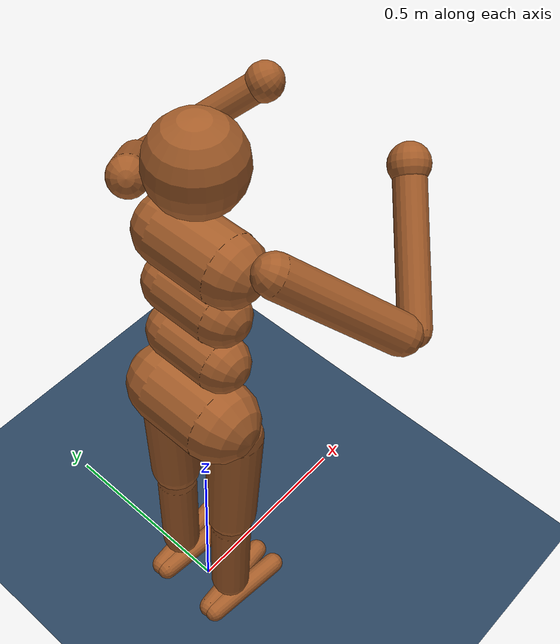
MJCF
<?xml version='1.0' encoding='utf-8'?>
<mujoco model="Humanoid">
  <option timestep="0.005" />

  <visual>
    <map force="0.1" zfar="30" />
    <rgba haze="0.15 0.25 0.35 1" />
    <global offwidth="2560" offheight="1440" elevation="-20" azimuth="120" />
  </visual>

  <statistic center="0 0 0.7" />

  <asset>
    <texture type="skybox" builtin="gradient" rgb1=".3 .5 .7" rgb2="0 0 0" width="32" height="512" />
    <texture name="body" type="cube" builtin="flat" mark="cross" width="128" height="128" rgb1="0.8 0.6 0.4" rgb2="0.8 0.6 0.4" markrgb="1 1 1" />
    <material name="body" texture="body" texuniform="true" rgba="0.8 0.6 .4 1" />
    <texture name="grid" type="2d" builtin="checker" width="512" height="512" rgb1=".1 .2 .3" rgb2=".2 .3 .4" />
    <material name="grid" texture="grid" texrepeat="1 1" texuniform="true" reflectance=".2" />
  </asset>

  <default>
    <motor ctrlrange="-1 1" ctrllimited="true" />
    <default class="body">

      <geom type="capsule" condim="1" friction=".7" solimp=".9 .99 .003" solref=".015 1" material="body" group="1" />
      <default class="thigh">
        <geom size=".06" />
      </default>
      <default class="shin">
        <geom fromto="0 0 0 0 0 -.3" size=".049" />
      </default>
      <default class="foot">
        <geom size=".027" />
        <default class="foot1">
          <geom fromto="-.07 -.01 0 .14 -.03 0" />
        </default>
        <default class="foot2">
          <geom fromto="-.07 .01 0 .14  .03 0" />
        </default>
      </default>
      <default class="arm_upper">
        <geom size=".04" />
      </default>
      <default class="arm_lower">
        <geom size=".031" />
      </default>
      <default class="hand">
        <geom type="sphere" size=".04" />
      </default>

      <joint type="hinge" damping=".2" stiffness="1" armature=".01" limited="true" solimplimit="0 .99 .01" />
      <default class="joint_big">
        <joint damping="5" stiffness="10" />
        <default class="hip_x">
          <joint range="-30 10" />
        </default>
        <default class="hip_z">
          <joint range="-60 35" />
        </default>
        <default class="hip_y">
          <joint axis="0 1 0" range="-150 20" />
        </default>
        <default class="joint_big_stiff">
          <joint stiffness="20" />
        </default>
      </default>
      <default class="knee">
        <joint pos="0 0 .02" axis="0 -1 0" range="-160 2" />
      </default>
      <default class="ankle">
        <joint range="-50 50" />
        <default class="ankle_y">
          <joint pos="0 0 .08" axis="0 1 0" stiffness="6" />
        </default>
        <default class="ankle_x">
          <joint pos="0 0 .04" stiffness="3" />
        </default>
      </default>
      <default class="shoulder">
        <joint range="-85 60" />
      </default>
      <default class="elbow">
        <joint range="-100 50" stiffness="0" />
      </default>
    </default>
  </default>

  <worldbody>
    <geom name="floor" size="0 0 .05" type="plane" material="grid" condim="3" />
    <light name="spotlight" mode="targetbodycom" target="torso" diffuse=".8 .8 .8" specular="0.3 0.3 0.3" pos="0 -6 4" cutoff="30" />
    <light name="top" pos="0 0 2" mode="trackcom" />
    <body name="torso" pos="0 0 1.282" childclass="body">
      <camera name="back" pos="-3 0 1" xyaxes="0 -1 0 1 0 2" mode="trackcom" />
      <camera name="side" pos="0 -3 1" xyaxes="1 0 0 0 1 2" mode="trackcom" />
      <freejoint name="root" />
      <geom name="torso" fromto="0 -.07 0 0 .07 0" size=".07" />
      <geom name="waist_upper" fromto="-.01 -.06 -.12 -.01 .06 -.12" size=".06" />
      <body name="head" pos="0 0 .19">
        <geom name="head" type="sphere" size=".09" />
        <camera name="egocentric" pos=".09 0 0" xyaxes="0 -1 0 .1 0 1" fovy="80" />
      </body>
      <body name="waist_lower" pos="-.01 0 -.26">
        <geom name="waist_lower" fromto="0 -.06 0 0 .06 0" size=".06" />
        <joint name="abdomen_z" pos="0 0 .065" axis="0 0 1" range="-45 45" class="joint_big_stiff" />
        <joint name="abdomen_y" pos="0 0 .065" axis="0 1 0" range="-75 30" class="joint_big" />
        <body name="pelvis" pos="0 0 -.165">
          <joint name="abdomen_x" pos="0 0 .1" axis="1 0 0" range="-35 35" class="joint_big" />
          <geom name="butt" fromto="-.02 -.07 0 -.02 .07 0" size=".09" />
          <body name="thigh_right" pos="0 -.1 -.04">
            <joint name="hip_x_right" axis="1 0 0" class="hip_x" />
            <joint name="hip_z_right" axis="0 0 1" class="hip_z" />
            <joint name="hip_y_right" class="hip_y" />
            <geom name="thigh_right" fromto="0 0 0 0 .01 -.34" class="thigh" />
            <body name="shin_right" pos="0 .01 -.4">
              <joint name="knee_right" class="knee" />
              <geom name="shin_right" class="shin" />
              <body name="foot_right" pos="0 0 -.39">
                <joint name="ankle_y_right" class="ankle_y" />
                <joint name="ankle_x_right" class="ankle_x" axis="1 0 .5" />
                <geom name="foot1_right" class="foot1" />
                <geom name="foot2_right" class="foot2" />
              </body>
            </body>
          </body>
          <body name="thigh_left" pos="0 .1 -.04">
            <joint name="hip_x_left" axis="-1 0 0" class="hip_x" />
            <joint name="hip_z_left" axis="0 0 -1" class="hip_z" />
            <joint name="hip_y_left" class="hip_y" />
            <geom name="thigh_left" fromto="0 0 0 0 -.01 -.34" class="thigh" />
            <body name="shin_left" pos="0 -.01 -.4">
              <joint name="knee_left" class="knee" />
              <geom name="shin_left" fromto="0 0 0 0 0 -.3" class="shin" />
              <body name="foot_left" pos="0 0 -.39">
                <joint name="ankle_y_left" class="ankle_y" />
                <joint name="ankle_x_left" class="ankle_x" axis="-1 0 -.5" />
                <geom name="foot1_left" class="foot1" />
                <geom name="foot2_left" class="foot2" />
              </body>
            </body>
          </body>
        </body>
      </body>
      <body name="upper_arm_right" pos="0 -.17 .06">
        <joint name="shoulder1_right" axis="2 1 1" class="shoulder" />
        <joint name="shoulder2_right" axis="0 -1 1" class="shoulder" />
        <geom name="upper_arm_right" fromto="0 0 0 .16 -.16 -.16" class="arm_upper" />
        <body name="lower_arm_right" pos=".18 -.18 -.18">
          <joint name="elbow_right" axis="0 -1 1" class="elbow" />
          <geom name="lower_arm_right" fromto=".01 .01 .01 .17 .17 .17" class="arm_lower" />
          <body name="hand_right" pos=".18 .18 .18">
            <geom name="hand_right" zaxis="1 1 1" class="hand" />
          </body>
        </body>
      </body>
      <body name="upper_arm_left" pos="0 .17 .06">
        <joint name="shoulder1_left" axis="-2 1 -1" class="shoulder" />
        <joint name="shoulder2_left" axis="0 -1 -1" class="shoulder" />
        <geom name="upper_arm_left" fromto="0 0 0 .16 .16 -.16" class="arm_upper" />
        <body name="lower_arm_left" pos=".18 .18 -.18">
          <joint name="elbow_left" axis="0 -1 -1" class="elbow" />
          <geom name="lower_arm_left" fromto=".01 -.01 .01 .17 -.17 .17" class="arm_lower" />
          <body name="hand_left" pos=".18 -.18 .18">
            <geom name="hand_left" zaxis="1 -1 1" class="hand" />
          </body>
        </body>
      </body>
    </body>
  </worldbody>

  <contact>
    <exclude body1="waist_lower" body2="thigh_right" />
    <exclude body1="waist_lower" body2="thigh_left" />
  </contact>

  <tendon>
    <fixed name="hamstring_right" limited="true" range="-0.3 2">
      <joint joint="hip_y_right" coef=".5" />
      <joint joint="knee_right" coef="-.5" />
    </fixed>
    <fixed name="hamstring_left" limited="true" range="-0.3 2">
      <joint joint="hip_y_left" coef=".5" />
      <joint joint="knee_left" coef="-.5" />
    </fixed>
  </tendon>

  <actuator>
    <motor name="abdomen_z" gear="40" joint="abdomen_z" />
    <motor name="abdomen_y" gear="40" joint="abdomen_y" />
    <motor name="abdomen_x" gear="40" joint="abdomen_x" />
    <motor name="hip_x_right" gear="40" joint="hip_x_right" />
    <motor name="hip_z_right" gear="40" joint="hip_z_right" />
    <motor name="hip_y_right" gear="120" joint="hip_y_right" />
    <motor name="knee_right" gear="80" joint="knee_right" />
    <motor name="ankle_y_right" gear="20" joint="ankle_y_right" />
    <motor name="ankle_x_right" gear="20" joint="ankle_x_right" />
    <motor name="hip_x_left" gear="40" joint="hip_x_left" />
    <motor name="hip_z_left" gear="40" joint="hip_z_left" />
    <motor name="hip_y_left" gear="120" joint="hip_y_left" />
    <motor name="knee_left" gear="80" joint="knee_left" />
    <motor name="ankle_y_left" gear="20" joint="ankle_y_left" />
    <motor name="ankle_x_left" gear="20" joint="ankle_x_left" />
    <motor name="shoulder1_right" gear="20" joint="shoulder1_right" />
    <motor name="shoulder2_right" gear="20" joint="shoulder2_right" />
    <motor name="elbow_right" gear="40" joint="elbow_right" />
    <motor name="shoulder1_left" gear="20" joint="shoulder1_left" />
    <motor name="shoulder2_left" gear="20" joint="shoulder2_left" />
    <motor name="elbow_left" gear="40" joint="elbow_left" />
  </actuator>

  <keyframe>

    <key name="squat" qpos="0 0 0.596                0.988015 0 0.154359 0                0 0.4 0                -0.25 -0.5 -2.5 -2.65 -0.8 0.56                -0.25 -0.5 -2.5 -2.65 -0.8 0.56                0 0 0 0 0 0" />
    <key name="stand_on_left_leg" qpos="0 0 1.21948                0.971588 -0.179973 0.135318 -0.0729076                -0.0516 -0.202 0.23                -0.24 -0.007 -0.34 -1.76 -0.466 -0.0415                -0.08 -0.01 -0.37 -0.685 -0.35 -0.09                0.109 -0.067 -0.7 -0.05 0.12 0.16" />
    <key name="prone" qpos="0.4 0 0.0757706                0.7325 0 0.680767 0                0 0.0729 0                0.0077 0.0019 -0.026 -0.351 -0.27 0                0.0077 0.0019 -0.026 -0.351 -0.27 0                0.56 -0.62 -1.752                0.56 -0.62 -1.752" />
    <key name="supine" qpos="-0.4 0 0.08122                0.722788 0 -0.69107 0                0 -0.25 0                0.0182 0.0142 0.3 0.042 -0.44 -0.02                0.0182 0.0142 0.3 0.042 -0.44 -0.02                0.186 -0.73 -1.73                0.186 -0.73 -1.73" />
  <key name="initial_pose" time="0.000" qpos="0.000908 -0.005007 1.282505 1.000000 0.000009 -0.000021 0.000010 0.007968 -0.008087 -0.004503 -0.005652 -0.007957 0.006827 -0.006791 0.000082 -0.005190 0.002654 -0.001959 0.006478 0.002623 0.006087 -0.006936 -0.008303 0.000662 0.000462 -0.006762 0.001806 0.009245" qvel="0.010438 -0.000184 -0.045227 0.003638 -0.008271 0.003918 -0.005703 0.002758 0.005895 -0.014147 -0.015039 -0.002537 -0.110209 -0.418606 0.068982 0.001956 0.007402 0.012972 -0.092698 -0.408815 0.002413 0.002381 -0.010025 -0.006914 0.022799 0.000230 -0.005445" /><key time="0.000" qpos="0.000908 -0.005007 1.282505 1.000000 0.000009 -0.000021 0.000010 0.007968 -0.008087 -0.004503 -0.005652 -0.007957 0.006827 -0.006791 0.000082 -0.005190 0.002654 -0.001959 0.006478 0.002623 0.006087 -0.006936 -0.008303 0.000662 0.000462 -0.006762 0.001806 0.009245" qvel="0.010438 -0.000184 -0.045227 0.003638 -0.008271 0.003918 -0.005703 0.002758 0.005895 -0.014147 -0.015039 -0.002537 -0.110209 -0.418606 0.068982 0.001956 0.007402 0.012972 -0.092698 -0.408815 0.002413 0.002381 -0.010025 -0.006914 0.022799 0.000230 -0.005445" /><key time="0.025" qpos="-0.049922 -0.000301 1.284435 0.982464 0.056429 0.071140 0.162846 -0.402641 -0.553527 -0.035999 0.004062 -0.057063 0.369532 0.049940 -0.046121 -0.925612 0.152138 0.333181 0.159696 -0.695667 -0.452460 -0.395679 -0.391874 0.342084 -1.796301 0.817021 0.836441 -1.860268" qvel="0.216880 0.342435 -0.030617 2.259912 2.655772 2.803690 -10.719625 -4.331475 0.217322 3.388257 7.101229 -0.641098 0.267079 -26.192707 2.423320 -1.868031 -2.605009 3.958276 5.463677 -17.775000 -23.785740 -2.205919 -2.445573 1.615732 11.678939 1.357398 4.058353" /><key time="0.050" qpos="-0.024054 0.027459 1.253599 0.984311 0.075901 0.154540 0.038574 -0.873115 -0.764580 0.261466 0.141308 0.341942 0.455030 0.136041 -1.008592 -0.886497 0.041341 0.530070 0.148918 -1.000640 -0.090492 -0.014139 0.125589 0.459494 -1.791357 0.755913 0.421770 -1.083900" qvel="0.185184 -0.075334 -0.099945 -0.001482 -1.666091 -2.219660 0.963220 3.419005 -2.265658 2.009769 5.288008 -2.705465 0.226055 3.441927 0.801021 -5.337079 -5.085471 -4.258007 -4.956086 -11.630383 -35.125198 6.692307 -4.704097 2.325718 -5.629284 -3.422238 -7.117436" /><key time="0.075" qpos="0.026216 0.031567 1.233479 0.951484 0.081157 0.280381 -0.097354 -0.577251 -0.985116 0.304217 0.187246 0.448037 0.366342 0.050851 -0.881835 -0.896497 0.037145 0.622401 0.377816 0.059293 -0.007943 -0.231677 0.743113 -0.703604 -0.037278 0.783206 0.253195 -1.764624" qvel="0.419886 0.284817 -0.068844 1.293581 0.818091 -0.156707 -2.023679 -0.537787 1.078835 -0.499177 1.641367 -0.452371 -0.009972 -0.189736 0.818058 2.668769 -0.577924 -0.400489 -0.693886 -11.695592 -6.367426 0.456986 -9.195827 5.698511 6.453800 -4.101000 0.576956" /><key time="0.100" qpos="0.030170 0.095992 1.219354 0.930680 0.081493 0.269406 -0.233696 -0.681970 -0.952463 0.452148 0.184234 0.547582 0.336488 0.052129 -0.918962 -0.888724 0.177342 0.354600 0.359353 0.047804 0.344868 -0.764059 0.398541 -0.622258 -0.447953 1.059341 0.616328 -1.769391" qvel="-0.112648 0.331083 -0.069448 0.343995 -0.421200 -1.725908 -0.059588 1.571375 0.786111 0.522051 5.033939 -0.342905 0.195211 -3.867334 -0.777843 -0.311199 1.415931 -0.128916 0.093797 -17.073967 5.779740 -0.500582 3.329535 -3.038249 -0.477078 2.763709 0.795543" /><key time="0.125" qpos="-0.020087 0.162720 1.218319 0.926874 0.052304 0.223630 -0.296914 -0.531206 -0.935668 0.437526 0.168077 0.639337 0.366239 0.048412 -0.836878 -0.902284 0.190536 0.240507 0.326158 0.044004 0.127866 -0.578288 0.697616 -0.407265 -0.300246 0.999964 0.911223 -1.754210" qvel="-0.528950 0.597144 -0.092623 0.485622 -0.474016 -1.900822 1.531436 -0.365840 0.646891 -0.836486 0.581402 -0.273583 -0.127006 2.492901 -0.349301 -0.373981 -3.659699 -0.656820 0.115816 -7.604551 18.641309 1.050254 4.345190 2.974518 -4.157684 1.694987 0.002982" /><key time="0.150" qpos="-0.087916 0.269583 1.143109 0.942897 0.101484 0.170574 -0.267490 -0.703281 -0.999566 0.267070 0.177164 0.359399 0.186787 0.050180 -0.953203 -0.916854 -0.067427 0.331582 -0.371964 -1.356741 -0.982449 0.997321 -0.027134 0.424110 -0.673006 1.013630 1.072079 -1.951711" qvel="-0.484996 1.169754 -1.896507 0.808345 0.728454 0.883434 -4.417845 -3.537334 1.548431 1.273830 -7.219769 1.361999 1.959766 -0.052725 0.210632 -4.783640 4.034305 -12.077057 -25.095176 -0.705915 34.394534 -12.515660 15.944041 -31.838419 3.046845 10.222951 -20.703350" /><key time="0.175" qpos="-0.153291 0.418515 1.017355 0.882289 0.039627 0.113546 -0.455085 -0.470320 -1.235182 0.386682 0.149249 0.195621 0.326353 0.049845 -0.820585 0.070468 0.214832 0.398628 0.009628 -2.383467 0.327604 -0.761498 0.336736 0.958927 -1.789753 0.997086 0.844396 -1.847904" qvel="-0.862420 1.146921 -0.347495 -2.090123 -2.607854 -5.417964 7.244900 3.805595 1.498732 -3.548282 3.545922 -2.019030 0.009788 -17.521557 -1.772816 -1.140008 -1.410251 -1.436294 15.423062 13.186436 -16.412204 10.708335 -3.537379 1.392097 -4.263169 -0.491940 -4.087155" /><key time="0.200" qpos="-0.266780 0.573365 0.852352 0.899696 -0.071023 -0.002492 -0.430692 -0.255678 -1.058967 0.138573 0.200116 0.590811 0.138070 -0.419272 -0.910839 -0.900931 -0.098604 0.637553 0.408300 -1.464011 -0.544737 -0.983847 -0.027532 0.403657 -1.606630 1.056543 0.708508 -1.754499" qvel="-1.392399 1.161854 -2.332991 0.550432 1.714288 3.259628 -0.583065 -5.937123 0.098960 1.723071 7.586024 2.854096 0.014110 0.874638 1.300760 -4.412822 0.040576 -2.102858 12.912806 35.836340 1.119545 -7.756744 12.587272 -39.145829 0.312590 5.346244 0.128430" /><key time="0.225" qpos="-0.468184 0.691582 0.594490 0.841738 0.001281 -0.189644 -0.505480 -0.269895 -1.030636 0.361886 0.182150 0.625443 0.303161 0.056855 -0.813390 -0.789547 0.092532 0.617600 0.417475 -1.252153 0.084917 -0.974401 0.187444 0.446449 -0.650551 0.594936 0.630360 -1.761592" qvel="-2.371498 0.975128 -2.637783 2.163086 -4.077128 -4.953155 7.905440 1.374950 0.236680 -2.226413 0.003651 3.307488 -0.907555 -17.801428 5.830857 0.621688 0.101015 -1.588322 9.183815 22.831189 -2.915354 9.921691 12.513419 -20.614705 -3.139871 -4.235063 0.398530" /><key time="0.250" qpos="-0.743786 0.772674 0.190386 0.764957 0.025509 -0.544672 -0.342816 -0.182684 -0.633591 0.151434 -0.249415 0.441365 0.149184 0.057444 -0.887633 -0.900937 0.099506 0.502303 0.290705 -0.304327 -0.215496 -0.667770 1.087520 0.781871 -1.764586 1.109507 0.332200 -1.757106" qvel="-1.812864 0.443515 -3.806704 5.126076 -7.460238 6.147866 8.979656 3.349627 -9.129844 -4.953207 -8.077659 5.621656 -1.239472 0.070422 0.443234 -0.172776 -4.170785 -10.815116 -12.315859 -25.534535 -0.839036 -1.327219 -3.282007 0.581958 -0.412113 -2.252207 0.068252" /><key time="0.275" qpos="-0.776328 0.825419 0.121866 0.739510 -0.241929 -0.625990 0.052278 -0.569530 -0.314061 -0.028949 -0.516977 0.442850 0.124870 0.070732 -0.928569 -0.898681 0.169174 0.680409 -0.308445 -0.449448 -1.202594 1.043945 1.011802 1.160374 -1.729422 1.064678 0.318570 -1.754929" qvel="0.099926 0.499606 1.266077 1.358797 1.368408 3.318291 -13.107896 2.972880 6.942068 -11.412764 6.614107 -14.947831 0.507851 2.413806 -1.436120 -0.982324 1.704358 -9.787538 1.312587 -0.713380 -5.304778 7.721064 0.320998 11.664316 0.178921 0.368948 -0.021158" /><key time="0.300" qpos="-0.750268 0.893438 0.162729 0.800852 -0.352612 -0.432223 0.217908 -0.797769 -0.643538 -0.240179 -0.084647 0.229160 0.353114 -0.211886 -0.842300 -0.885480 0.022083 0.591443 -0.112845 -0.022099 0.467170 -0.940950 1.071385 0.998140 -1.235192 0.941684 0.665837 -1.753392" qvel="0.101129 0.690099 0.080794 -1.938889 1.842475 -0.299287 1.975720 3.633085 2.873843 -0.629021 -2.118135 -4.468887 -9.807496 -12.246335 0.230857 -0.655629 -1.330484 -0.412542 6.660241 -23.133692 2.220190 0.665478 -6.201894 9.126989 -2.533451 2.719153 -0.006208" /><key time="0.325" qpos="-0.730888 0.960624 0.158960 0.773493 -0.418837 -0.452681 0.146165 -0.778171 -0.302668 -0.124228 -0.041526 0.427790 0.181436 0.200950 -0.654521 -0.880698 -0.096909 0.163226 -0.026907 0.044537 -0.263507 -0.874963 0.773625 0.768835 -1.215934 0.868554 0.678247 -1.911798" qvel="0.073935 0.134827 0.099153 1.489230 0.973996 0.365489 1.237646 -3.059663 -0.075561 -0.732995 4.332314 2.954928 5.478687 -18.717039 0.067376 1.727279 -1.532315 4.685157 0.026833 17.067056 0.249077 -8.068999 -3.794310 3.740213 1.191109 0.330997 -3.772616" /><key time="0.350" qpos="-0.698777 0.980502 0.167247 0.851408 -0.382505 -0.354406 0.056482 -0.613562 -0.754388 0.075954 0.115814 0.649353 0.373590 0.137124 0.323245 -0.883276 0.177358 0.629231 0.285775 -0.030870 0.235257 -0.642171 0.275307 0.724229 -1.418760 0.883179 0.886889 -1.753440" qvel="0.412725 0.147940 0.071026 0.473815 3.307392 -3.279920 1.020048 -1.889635 5.295278 -2.962310 0.839756 -0.464305 7.201567 29.749065 -0.022554 1.331494 0.703957 -6.642554 -4.075472 24.564280 -16.101572 -0.175089 7.863934 -9.473178 -3.773699 1.968589 0.058290" /><key time="0.375" qpos="-0.688059 0.976122 0.149423 0.841321 -0.346223 -0.414909 0.012623 -0.795682 -0.647066 0.125892 0.133642 0.458031 -0.252838 -1.266053 -0.953694 -0.888990 0.187784 0.636290 0.310201 -0.154408 -0.549460 -0.544064 0.789723 0.712265 0.299903 1.060829 0.523714 -1.752704" qvel="0.244991 -0.058379 -0.899163 -0.883026 -0.955396 -1.309811 0.904517 -0.593727 -1.109151 2.353927 5.417969 -6.886459 -20.834387 -6.679446 -1.807245 -0.294530 1.659904 -3.213750 -17.094686 -22.146920 -6.612799 -4.440311 3.672359 26.848317 -0.504417 -3.956796 0.042250" /><key time="0.400" qpos="-0.707525 0.973949 0.132296 0.784113 -0.413549 -0.461567 -0.033154 -0.561559 -0.695891 0.330403 0.071201 0.620146 0.446782 0.339052 0.702668 -0.679085 0.248885 0.565920 0.054238 -0.851145 0.124109 -0.892979 -0.149909 0.062523 0.889168 0.936614 0.244223 -1.753122" qvel="0.162117 0.155850 -0.189646 -3.925831 -1.382746 3.541357 -5.508905 2.193343 6.988179 0.830075 3.878767 2.945930 -0.539006 29.821870 9.141819 1.914700 2.055792 0.994603 11.798003 44.225786 0.738206 -8.762692 -28.010806 -0.625367 -1.303088 3.168495 -0.086379" /><key time="0.425" qpos="-0.697994 0.945408 0.141257 0.815628 -0.363503 -0.445847 -0.061951 -0.483045 -0.727252 0.451754 -0.013344 0.644144 0.379845 0.043348 -0.276882 -0.893545 0.150738 0.084307 -0.068129 0.109680 0.760196 -0.757324 -1.545838 -0.400617 -1.232370 0.630705 0.801966 -1.754750" qvel="-0.102786 -0.194014 -0.171260 1.007864 -0.147719 -4.607137 6.096786 0.798079 -0.502555 -1.831456 -0.070047 -0.357594 -0.174458 -19.072612 0.336774 0.951832 2.373725 -3.705112 -2.185007 10.858158 23.290773 1.156967 13.448921 -31.855430 -4.911758 2.826977 0.075470" /><key time="0.450" qpos="-0.739245 0.905869 0.119696 0.775358 -0.240632 -0.581424 -0.053491 -0.585966 -0.414600 0.293964 0.000797 0.534414 0.290472 0.085334 -0.890630 -0.884857 0.187539 0.412325 0.125730 -0.168195 -0.614619 0.577620 -1.267582 0.271386 -1.754777 1.118121 0.888239 -1.754091" qvel="-0.390512 -0.425807 -0.335604 -0.290377 -3.797474 -3.196617 0.765967 3.718090 -1.828309 3.337010 -0.706867 3.975134 -0.482266 0.560518 0.145703 -0.591886 -4.178215 11.237516 23.821744 6.353736 -21.663910 9.102081 5.944050 0.401995 -0.567336 0.920507 0.044875" /><key time="0.475" qpos="-0.748172 0.862268 0.092045 0.696985 -0.146687 -0.697391 -0.079625 -0.468385 -0.265667 -0.023236 0.109938 0.235117 0.003863 -0.534586 -0.941004 -0.949982 0.194668 0.463914 0.321582 -0.377185 -0.272135 0.453256 -0.103410 0.470710 -1.927929 1.061902 1.060985 -1.758955" qvel="0.197878 0.078030 -0.257073 1.245138 1.214994 -0.716133 5.612279 -6.038573 -5.097921 4.505347 -5.246881 8.792106 13.729072 1.699833 3.044782 -1.040134 6.267915 -0.856003 -25.399888 -37.187117 43.243459 2.696122 -0.404621 -7.415985 -0.115474 -0.552525 -0.004366" /><key time="0.500" qpos="-0.758536 0.862686 0.086355 0.717171 -0.162292 -0.673173 -0.078523 -0.692914 -0.564415 0.088792 0.077746 0.241523 0.394018 0.023500 -0.369305 -0.835040 0.181820 0.319247 0.055936 -1.564762 -0.857638 0.579610 0.433812 -0.140642 -1.753169 0.950886 0.839524 -1.959008" qvel="-0.744798 -0.062933 0.016799 1.625766 0.436850 1.180996 -6.931855 -2.385349 -0.960324 2.205855 2.628054 -2.358680 -0.821661 35.229387 -32.781276 -0.018566 1.843558 7.588894 17.109035 3.806166 -20.287121 3.364518 -5.410594 0.349224 -0.018450 -0.947218 -1.544581" /><key time="0.525" qpos="-0.806236 0.840865 0.093157 0.698117 -0.110051 -0.699756 -0.104220 -0.641757 -0.387146 -0.166025 0.133053 0.607660 0.295146 0.085358 -0.937826 -0.887238 -0.010651 0.188754 0.251247 0.110358 0.057691 -0.913763 0.788295 -0.612013 -0.758667 1.055957 0.738999 -1.752864" qvel="-0.144402 -0.225574 0.303904 0.010838 -0.137660 -0.021910 1.358759 3.035551 0.567367 -3.104409 6.673426 -0.787119 -1.493209 2.217478 -0.171498 1.977744 -2.931372 -6.296574 -2.322415 -13.137283 -2.007140 2.596420 -5.066858 20.205394 -0.223259 1.401077 0.110576" /><key time="0.550" qpos="-0.804488 0.802991 0.110031 0.720630 -0.177526 -0.666415 -0.071188 -0.736320 -0.488046 -0.175902 0.234148 0.561637 0.467037 0.221241 0.028136 -0.892600 0.226000 0.353883 0.086653 -1.234557 -0.906842 -0.896886 0.770891 -0.300928 -0.045856 0.840768 1.093533 -1.766118" qvel="-0.151179 -0.287374 -0.481719 -2.070783 0.492670 -1.469859 -3.761148 -0.083229 6.395240 -0.725116 4.613111 -0.024992 -2.068781 2.636558 0.285386 0.528263 -6.559391 -0.363345 -4.737026 -0.015140 0.158463 -4.633051 9.479944 -4.736216 -13.456921 -0.730971 0.065715" /><key time="0.575" qpos="-0.769459 0.774970 0.102843 0.728342 -0.271342 -0.628463 0.030430 -0.709991 -0.425315 -0.421477 0.165806 0.025130 0.239686 -0.249135 -0.955188 -0.882388 0.017376 0.586657 -0.504914 -1.960400 1.130988 -0.717112 -0.916593 -0.056878 0.018164 1.132748 0.936044 -1.758712" qvel="0.524586 -0.345783 -0.172061 2.052531 3.577633 -1.615832 4.019457 -10.017157 1.855261 -0.456406 4.109579 12.658953 16.686717 6.588078 -0.375464 6.327616 0.017991 2.618181 -9.544135 -3.497940 10.715593 -12.918012 7.451025 -28.858585 -1.438635 1.856071 0.071597" /><key time="0.600" qpos="-0.778285 0.761624 0.107654 0.736336 -0.237363 -0.630690 -0.060808 -0.683216 -0.373096 -0.075723 0.040856 0.455525 0.204027 0.043359 -0.647994 -0.696256 0.161934 0.660334 -0.645454 -1.185164 0.229634 -0.609068 -1.360842 0.144485 -0.235062 1.061011 0.788843 -1.985746" qvel="-0.326991 -0.311251 0.313243 -0.592109 -1.448103 -0.484055 -1.794444 3.570154 1.482965 -6.068796 -11.464399 -4.132381 -0.657244 4.625720 11.995280 -3.254851 1.508337 0.280388 14.114020 0.436608 15.242402 -6.713275 -3.034685 28.735326 -0.283315 -0.705084 -7.089487" /><key time="0.625" qpos="-0.787748 0.726487 0.106901 0.683616 -0.169860 -0.695802 -0.140274 -0.766663 -0.237632 -0.055817 -0.082664 0.696757 -0.001293 -0.347998 -0.859906 -0.905090 -0.023886 0.316734 -0.394436 0.193766 -1.019893 -0.975854 -1.324204 0.484092 0.611774 1.070035 0.377569 -1.778212" qvel="-0.039665 -0.302233 -0.123854 0.027340 -0.906104 -4.095566 -1.359998 0.073459 -0.080812 -1.786776 1.432771 -13.748010 -22.585018 2.080830 0.531235 -3.037482 -3.193510 5.233596 16.977191 -21.997912 2.307109 12.031520 0.922404 -20.080051 -0.001117 -1.697506 0.849947" /><key time="0.650" qpos="-0.765990 0.702799 0.113817 0.683010 -0.016699 -0.697005 -0.217723 -0.717101 -0.839137 0.025874 -0.020547 0.151422 0.355357 0.017666 -0.917506 -0.909623 0.197964 0.330309 -0.162790 -2.841980 -0.590767 1.016689 -0.817686 1.114226 -2.053687 0.985431 0.216263 -1.755078" qvel="0.166160 -0.358466 0.457983 1.045562 3.657680 -6.036993 6.476537 -6.079545 -2.493291 6.120345 4.766464 -1.261141 -3.539784 0.676187 -0.736129 -1.014454 5.050806 15.721082 -32.344214 26.869472 -5.490121 -7.487881 -2.403596 21.928562 -1.895423 3.006459 0.025366" /><key time="0.675" qpos="-0.819929 0.703287 0.133893 0.646996 0.077998 -0.687485 -0.320433 -0.825620 -0.753435 0.210121 0.057155 0.476649 0.222608 0.065031 -0.896276 -0.886263 0.115298 0.405817 0.190678 -1.637389 -0.914748 0.688850 -0.677152 0.642036 -0.920883 1.077747 0.493366 -1.755127" qvel="-0.788606 -0.081156 -0.022345 -0.678135 0.879700 -0.085401 -1.254200 5.785367 4.084784 -5.121779 7.394552 -6.391947 0.182361 1.353966 -1.385925 -2.732720 -0.571638 -9.791051 15.938275 -23.137718 -17.407615 1.950877 -3.887596 10.443181 2.432224 2.115432 -0.038346" /><key time="0.700" qpos="-0.772018 0.696272 0.124919 0.688393 -0.025313 -0.668000 -0.281514 -0.721388 -0.815136 -0.004092 0.180597 0.131845 0.245472 -0.805239 -0.502843 -0.881099 0.093173 0.480621 0.030840 -0.559764 0.583265 -0.843656 -1.053431 0.357962 -1.198232 1.000519 1.005883 -1.493646" qvel="-0.172884 0.093647 0.302438 -2.441134 -2.516654 2.109021 -4.273996 7.792194 1.281520 -0.001355 2.144587 -2.723223 12.034183 24.836746 -0.043415 1.040477 4.271967 -7.584728 -0.158922 12.563724 -16.092689 1.851762 -17.472919 37.996774 -2.472655 -5.083209 16.372061" /><key time="0.725" qpos="-0.759527 0.679527 0.113540 0.602108 -0.032761 -0.734514 -0.311258 -0.801634 -0.546659 -0.157398 0.159921 0.423933 0.154506 -0.362460 -0.352653 -0.898755 0.185736 0.622562 -0.161183 0.108830 -0.325168 -0.822749 -1.424639 0.611968 0.873948 1.055202 0.804830 -0.825847" qvel="0.422095 -0.119171 0.438579 -0.550736 -0.512971 -2.221102 -0.385077 -1.916660 -1.321057 -2.213062 -8.278481 -3.782300 -18.088851 -24.893464 0.335686 -0.307583 -0.543299 1.993526 0.003178 -42.259171 -2.260780 1.229240 14.509270 13.178799 0.019355 2.721030 -1.158701" /><key time="0.750" qpos="-0.745462 0.650790 0.149527 0.592153 -0.000382 -0.703613 -0.392790 -0.664435 -0.652135 -0.236456 0.170216 -0.180285 0.433670 0.140197 -0.970322 -0.881854 0.229395 0.153753 -0.834475 -1.589942 -0.896795 0.715806 -1.490022 1.058471 0.398817 0.999442 0.691087 -1.768484" qvel="0.013489 -0.282418 0.233940 0.630548 0.018483 -0.589345 -2.326416 -2.422240 -0.619002 0.785220 -5.641147 -2.568174 -3.320124 2.212701 -0.196698 -1.699962 -7.818641 -3.803535 -20.537119 -2.153187 8.516482 0.113024 -0.296244 -9.376169 -2.674965 -6.566766 0.743140" /><key time="0.775" qpos="-0.770615 0.657506 0.152387 0.620813 0.070241 -0.678162 -0.386980 -0.600862 -0.967839 -0.103271 0.182606 0.308736 0.311449 0.246081 0.135554 -0.881917 0.152085 0.027620 -0.567029 -0.778349 0.219590 -0.789221 -1.535783 0.891726 -1.834856 0.911970 -0.061250 -1.815002" qvel="-0.303282 0.149008 -0.208218 -0.808035 0.323205 5.560816 -3.298852 0.849735 -3.220690 3.462405 8.437408 -1.861052 0.411842 -3.394722 -0.196989 -1.827108 -6.318076 3.562612 16.462492 6.900019 12.088319 1.360202 -11.258129 -2.888666 2.559952 -4.071927 2.380404" /><key time="0.800" qpos="-0.770161 0.658355 0.099575 0.627029 -0.127090 -0.721406 -0.265060 -0.804899 -0.854701 -0.331098 0.007080 0.140635 0.369714 0.048260 -0.696604 -0.891756 0.203069 0.044002 -0.497875 -0.447101 -0.771026 0.883308 -1.475149 0.147895 -1.754620 1.073293 -0.585876 -1.754572" qvel="0.093415 0.071200 0.130338 -0.951936 0.281515 2.896261 -0.528695 2.320575 -2.308606 2.030575 -0.166721 -0.623825 -0.268316 15.741431 0.502389 0.237483 5.863092 -1.952497 3.585027 26.472154 -3.738235 0.965003 -4.508406 0.012982 -0.711176 -2.797051 0.121810" /><key time="0.825" qpos="-0.755483 0.657773 0.099622 0.625382 -0.077148 -0.724263 -0.279981 -0.795223 -0.875877 -0.302586 0.112406 0.422917 0.354908 0.119856 -0.290806 -0.932067 0.173022 0.452513 -0.596237 0.038954 -0.882397 -0.080204 -1.345030 0.213774 -1.305199 1.069342 -0.599637 -1.754211" qvel="0.029410 -0.009401 0.005163 0.111644 0.129971 -0.532301 0.093471 0.046552 -0.216345 2.354019 1.745276 1.053566 -1.827882 -7.510015 1.338692 4.861202 -4.330302 -1.503431 -1.230587 -0.160029 7.482833 4.096559 -6.893914 28.586039 1.032404 2.153639 0.096232" /><key time="0.850" qpos="-0.753909 0.668328 0.098789 0.638371 -0.093991 -0.716977 -0.263803 -0.798178 -0.921871 -0.318888 0.087308 0.303473 0.368554 0.083828 -0.504252 -0.899681 0.170608 0.598129 -0.492710 0.060149 -0.474652 -0.988339 -0.966000 0.068491 0.131054 1.024450 -0.199321 -1.754462" qvel="-0.760077 0.195364 0.132498 -3.281151 -1.934176 3.681383 -0.321673 9.876806 -3.600601 -0.954332 -7.182752 0.562735 17.138971 -21.970285 -0.107304 -1.011578 -3.011794 -4.383634 0.487016 -0.057053 3.398077 11.992343 -9.214991 22.898140 -2.003781 1.266070 0.003835" /><key time="0.875" qpos="-0.759470 0.681950 0.102793 0.604961 -0.088410 -0.724675 -0.317886 -0.813491 -0.841976 -0.217052 0.077239 0.637172 0.345559 0.172322 -0.249783 -0.886015 0.185591 0.487201 -0.110248 0.052033 -0.793260 -0.839892 -0.674947 0.024479 0.893327 1.044002 -0.200024 -1.754011" qvel="0.101488 -0.023964 0.052765 -0.323777 -0.237268 -0.376735 0.873538 -0.044638 -1.129164 1.656872 -0.785801 0.600011 -3.371377 -3.727018 0.261997 -0.000008 -1.020582 2.385596 -2.594470 6.772411 8.578769 -2.073879 2.983590 -0.703082 0.520786 -1.083474 -0.015522" /><key time="0.900" qpos="-0.740278 0.658279 0.116624 0.595364 -0.076200 -0.721602 -0.345000 -0.787019 -0.985323 -0.327139 0.261292 0.404646 0.379313 -0.279301 -0.477080 -0.600401 0.186662 0.537554 0.021941 -2.115272 0.632717 0.775222 -1.505553 0.871183 -0.985533 1.055355 -0.416166 -1.754236" qvel="0.055441 0.137079 0.265881 -0.605298 -2.101174 0.587414 -6.230617 -1.386395 1.760676 -0.480475 -3.544666 0.831827 1.198955 1.979851 15.735791 0.281540 -4.344460 15.926961 -4.338629 43.108801 -9.728941 6.210650 5.788173 -7.526698 0.046989 -2.323029 0.003692" /><key time="0.925" qpos="-0.757419 0.672731 0.102991 0.653475 -0.096360 -0.679133 -0.320098 -0.671842 -0.938826 -0.044073 -0.179997 0.441654 0.394901 0.045760 -0.758331 -0.917818 0.188372 0.514112 0.366788 -1.713956 0.389490 -0.927342 -1.446002 0.896474 -0.166913 1.018881 -0.206841 -1.754149" qvel="0.074100 0.314829 -0.248298 -0.495617 -0.008159 6.246162 -2.378463 1.380050 -0.654447 -1.820904 -2.559275 1.201453 0.058872 13.681656 0.102325 -0.771312 0.050447 -0.154216 10.755273 -14.965986 -1.571844 3.018639 -4.742357 14.792402 4.272628 2.020325 -0.049721" /><key time="0.950" qpos="-0.735440 0.691096 0.101942 0.722675 -0.319993 -0.600545 -0.121206 -0.658868 -0.548384 -0.214362 -0.284532 0.687256 0.370427 0.048326 -0.672141 -0.898812 -0.108242 0.486711 -0.046639 -0.411932 -0.767247 0.134598 -1.069302 0.936330 -0.641654 0.857573 -0.411069 -1.823176" qvel="-0.211280 0.021809 0.575717 -0.902786 -0.100525 1.953184 7.553721 7.801797 -3.290260 0.601143 -0.609707 0.174626 -0.162726 -11.034660 0.254342 -3.354962 -8.555700 -3.616417 25.682424 14.293507 -0.707652 2.973848 3.767698 -8.845677 -2.195255 1.330327 -12.072682" /><key time="0.975" qpos="-0.667314 0.709553 0.149751 0.825952 -0.380929 -0.414411 0.030987 -0.667715 -0.615637 -0.448417 -0.189209 0.272164 0.364173 0.041262 -0.520226 -0.917672 0.191587 0.599984 0.241862 0.053447 0.490018 -1.081547 -1.529807 0.580645 -1.803242 0.997310 0.466470 -1.989052" qvel="0.570971 0.237593 0.267506 1.012442 4.434219 -1.071949 4.709752 -1.074261 -0.068207 -1.148801 -7.966271 -0.610030 0.233595 -13.809447 0.106999 1.598748 4.601158 2.336953 -0.302538 -16.876107 4.876059 -1.016986 -5.456130 2.116633 1.079131 12.073732 -6.122915" /><key time="1.000" qpos="-0.632693 0.748143 0.159448 0.807687 -0.448989 -0.382159 0.002131 -0.694088 -0.424308 -0.302376 -0.115344 0.377826 0.355012 0.048096 -0.710018 -0.880297 0.155604 0.391263 0.142923 0.086727 0.157961 0.667577 -0.817423 -0.183394 -1.370076 1.054860 0.975230 -1.194948" qvel="-0.082820 0.048753 -0.225267 -2.416060 -1.854077 2.959445 3.038550 5.843424 -0.875899 5.040974 9.599525 2.038579 -0.167531 -4.660113 0.480196 -0.260033 -8.354535 -4.998854 -0.860558 -6.085797 21.920823 5.618323 -10.183160 10.562716 -0.185818 8.647176 -13.218165" /><key time="1.025" qpos="-0.662591 0.747760 0.131421 0.782446 -0.433074 -0.444785 -0.048904 -0.646914 -0.432304 -0.346470 0.205199 0.638824 0.387971 0.050667 -0.777077 -0.917384 0.187862 0.307725 0.199275 0.067236 0.095313 -0.707470 0.050726 -0.387446 -0.294463 0.916017 0.951592 -1.783991" qvel="-0.052115 -0.196143 -0.269279 0.708970 3.638244 -0.304065 1.226968 -8.366032 2.263744 7.052851 -0.628477 10.933813 -0.709005 9.043635 1.044952 2.583027 2.355589 6.766579 -1.474978 -3.320566 -20.209225 5.391029 -1.452015 16.515210 3.354566 0.859407 1.227091" /><key time="1.050" qpos="-0.693264 0.722843 0.138970 0.775924 -0.368648 -0.498933 -0.114482 -0.730239 -0.423681 -0.220830 -0.126852 0.413407 0.127128 0.059306 -0.901211 -0.907107 0.197997 0.537259 -0.438601 -1.390070 -1.056805 0.688916 0.943907 0.262253 -1.613434 1.067093 0.575268 -1.754028" qvel="-0.527477 -0.435374 0.898373 0.363301 -1.075173 0.077165 -2.534200 3.919176 1.525037 -4.926974 4.915239 -5.948631 -0.389960 1.080021 0.213600 -0.746915 -4.769213 -11.877805 -9.705690 -10.312517 -21.973450 6.622046 0.214583 -3.250282 -0.578379 -5.344931 0.008481" /><key time="1.075" qpos="-0.745038 0.694165 0.177618 0.817510 -0.414072 -0.395346 -0.062634 -0.605361 -0.396743 -0.305449 -0.097058 0.394138 0.211659 0.179536 -0.001859 -0.899524 0.067516 0.603485 -0.716181 -0.541045 0.606419 -0.904638 0.889078 -0.064688 -0.831180 0.798283 0.567411 -1.649932" qvel="-0.194150 0.080587 -0.404536 -2.752691 2.936998 5.730934 1.925352 0.092136 2.449033 2.663309 4.020271 5.694645 -3.414789 11.228730 0.760354 6.786376 -0.386378 7.694953 23.558429 32.760102 2.702383 -4.393440 -8.349351 22.991844 0.549492 2.521071 6.545254" /><key time="1.100" qpos="-0.775477 0.672487 0.124494 0.755199 -0.419604 -0.500434 -0.056331 -0.678787 -0.336621 -0.488907 -0.122001 0.468775 -0.184509 -0.436805 -0.976278 -0.907315 -0.020688 0.561067 -0.924317 -0.642192 -0.535552 -0.889467 0.598395 0.218241 -1.762329 0.400805 0.412685 -1.304047" qvel="-0.106631 -0.434745 0.023739 0.862528 -1.320560 -1.435049 4.838810 -0.054368 -8.298364 7.675285 -9.689185 -1.360219 -11.550187 2.994455 0.346456 -10.957889 7.190609 -7.372319 -9.241520 25.053427 12.798244 -2.641319 2.658521 -0.143735 -0.582564 7.899630 -26.977551" /><key time="1.125" qpos="-0.780242 0.659326 0.132970 0.769357 -0.338713 -0.515825 -0.165193 -0.825474 -0.880520 -0.265361 0.027288 0.573808 0.380052 0.069405 -0.362448 -0.204654 0.197197 0.282826 -0.810188 -2.531540 0.039077 0.356717 0.427226 0.878728 -1.756485 0.411345 0.468964 -1.968057" qvel="-0.298706 0.256060 -0.276105 -2.659695 0.681418 -4.334097 1.066326 3.712438 7.674983 -2.482462 6.659635 -0.523703 -1.218707 -1.264129 -4.611059 -0.845421 6.998571 -6.498147 0.270687 23.636285 8.966201 2.441983 5.573976 0.008701 -3.452327 12.787752 -44.442321" /><key time="1.150" qpos="-0.807916 0.666140 0.094881 0.721337 -0.279461 -0.593670 -0.221652 -0.741200 -0.861555 -0.420379 -0.050673 0.610241 0.236218 -0.150943 -0.928816 -0.934584 0.013510 0.649040 -0.481643 -2.232328 1.090612 0.266583 -0.441572 0.873404 -1.754670 0.814714 -0.193313 -1.758575" qvel="0.095779 0.047144 -0.017191 -1.716050 -1.121042 2.199115 -1.165776 4.326568 -4.773311 2.376573 -4.549690 -5.087801 -3.186072 -6.815184 1.458238 -9.616934 2.449498 -6.781636 2.737121 9.645408 -18.819312 -12.368223 -6.919988 0.052907 5.321586 -4.055981 0.529690" /><key time="1.175" qpos="-0.826511 0.685106 0.084579 0.654647 -0.306456 -0.629421 -0.285220 -0.769326 -0.803809 -0.465347 0.126021 0.702574 0.355930 0.047051 -0.931754 -0.901004 0.224101 0.571151 0.386896 -0.786270 0.882839 -0.438615 -1.087897 0.233181 -1.236494 1.055559 -0.385978 -1.754717" qvel="-0.327402 -0.028619 0.247432 0.409667 -0.919331 -4.077653 -0.376909 -1.482092 1.005553 -0.312187 -1.012300 -1.202519 -0.686717 1.294504 0.306577 4.767316 1.128402 16.475388 38.912217 0.303624 17.929450 -4.629752 5.404249 -12.115089 1.640971 -0.001263 0.016462" /><key time="1.200" qpos="-0.868821 0.650225 0.131447 0.675509 -0.321959 -0.573149 -0.333961 -0.520084 -0.560342 -0.376756 0.023555 0.622204 0.209006 0.161877 -0.511948 -0.890659 0.209070 0.451860 0.236939 0.056339 1.001210 -0.221712 -1.474030 -0.305165 -1.810585 0.901617 -0.247514 -1.754613" qvel="-0.303374 -0.100030 -0.040207 -2.694846 2.336065 0.745996 3.684157 3.114760 4.157995 -1.938266 -0.326548 1.941258 7.666749 9.872762 -0.190800 -0.181374 -2.813389 -6.094755 -0.278576 -2.365714 28.838417 2.390875 -10.350428 2.660310 -3.659408 4.445842 -0.013077" /><key time="1.225" qpos="-0.878777 0.637877 0.087450 0.657320 -0.425930 -0.548840 -0.292044 -0.477581 -0.381352 -0.460953 0.022692 0.494034 -0.016082 -0.586505 -0.970712 -0.895498 0.200935 0.446281 0.230639 -0.179021 0.475420 -0.001790 -1.422669 -0.461771 -1.899012 1.078073 0.112273 -1.865151" qvel="-0.146979 0.020646 -0.227707 -0.441062 -1.655814 -2.132182 1.071104 1.808601 0.404095 -4.586447 -7.685328 -6.570729 -3.481902 2.541165 0.429860 -0.306747 0.827043 -6.888456 -14.065652 -16.902989 32.875595 5.837717 6.910965 1.703561 0.853273 -0.752742 3.263751" /><key time="1.250" qpos="-0.939705 0.654583 0.098680 0.545716 -0.370910 -0.620791 -0.423366 -0.438475 -0.314197 -0.324171 -0.024094 0.568886 -0.282111 0.103988 -0.889021 -0.882739 0.124714 0.282914 0.317159 0.078684 -0.670920 0.274127 -0.637417 0.361819 -1.300411 0.992586 0.271020 -1.758245" qvel="-0.451584 -0.052505 -0.114001 -0.418645 1.234144 -3.128319 6.389905 -0.570230 0.803955 -0.321310 1.221729 0.579491 -2.855470 0.281339 0.135461 -1.507511 -6.030892 -7.298227 -11.767700 -12.778629 0.891350 3.895051 20.955306 -33.561450 1.018141 5.163605 0.012461" /><key time="1.275" qpos="-0.964825 0.640876 0.093833 0.565848 -0.405895 -0.552353 -0.458227 -0.234193 -0.392912 -0.348688 0.168378 0.627250 -0.045492 -0.000531 -0.066437 -0.882869 0.154874 0.422227 0.384810 0.050288 -0.502018 -0.909422 -0.411636 0.627225 -1.044754 1.055618 0.789669 -1.774152" qvel="0.092378 -0.020060 0.096843 -1.261194 -2.598575 0.306750 -3.444988 4.147895 0.692746 -1.830937 -0.855174 -1.703791 -1.464686 -18.227800 0.046471 -1.979178 0.578534 0.931206 0.163191 -37.452110 0.869121 9.398171 -1.772218 9.125066 0.055955 -0.156302 0.949538" /><key time="1.300" qpos="-0.960115 0.598010 0.100227 0.646462 -0.511865 -0.478476 -0.301899 -0.510013 -0.300083 -0.626120 0.106328 0.312717 -0.463038 -1.487238 -0.826813 -0.882193 -0.045381 0.633295 -0.205737 -1.307120 -0.543947 -0.879894 -1.520248 0.627762 -0.223707 0.910226 1.031460 -1.475912" qvel="0.128460 -0.209364 -0.671602 0.080741 -1.191662 2.218686 -2.024359 -4.912738 -1.621784 2.115663 1.156698 5.818007 6.628082 20.725925 0.058899 5.422698 2.135602 8.869011 -3.191036 -6.176227 0.004630 -9.765664 6.285930 -18.895549 -9.379863 -3.530397 12.722858" /><key time="1.325" qpos="-0.959662 0.605119 0.114966 0.571397 -0.516157 -0.534752 -0.348035 -0.418368 -0.082061 -0.517786 -0.056662 0.237187 -0.245188 -0.151206 -1.103002 -0.892143 0.024092 0.508172 0.130076 -0.186860 -0.028485 -0.688609 -1.504034 1.029342 -0.179046 -0.583827 0.821041 -1.852143" qvel="0.272837 -0.189468 -0.060230 -1.800002 0.428719 1.944653 3.525787 5.106628 0.505425 1.387819 -7.925689 -8.701678 -24.888834 0.061385 0.304980 -1.939209 4.605563 -5.819272 -8.925780 -11.425120 -22.194143 -3.083594 -4.500415 2.990489 -6.473900 -0.424255 3.473150" /><key time="1.350" qpos="-0.946630 0.615578 0.120890 0.578770 -0.614772 -0.440253 -0.305381 -0.491845 0.169652 -0.444082 0.137958 0.535935 0.080363 0.082265 -0.053236 -0.884824 -0.147879 0.654255 -0.300666 -0.741713 -0.950450 -0.250706 -0.909688 0.651927 0.188117 -0.588068 0.704639 -1.825512" qvel="-0.003190 0.070967 0.037382 -0.219417 -0.660301 0.059720 1.843585 -0.028707 0.248455 2.438481 7.215540 13.591772 27.043890 16.481897 -0.267419 2.577439 6.214364 0.870242 -3.438076 0.900314 -24.733873 -0.064845 -1.856467 -8.630712 3.800787 -2.286181 -4.106035" /><key time="1.375" qpos="-0.956928 0.636510 0.134880 0.566003 -0.657510 -0.390390 -0.308086 -0.324975 0.255644 -0.225567 0.104348 0.628374 -0.012024 -0.365842 -0.966486 -0.902666 0.081061 0.668233 -0.050521 -0.026665 0.271091 -0.895993 -0.817369 0.235975 -0.132271 -0.297936 0.433092 -1.754063" qvel="0.313481 -0.009869 0.508958 0.360085 2.685584 3.850632 -3.131498 1.495012 -2.392113 -0.120177 5.299766 -6.014445 -0.999404 2.681131 -1.750481 -7.404055 -0.308871 -9.376655 -6.564228 -0.584306 0.644642 -8.913265 -9.738043 8.015473 2.782897 2.139379 -0.002942" /><key time="1.400" qpos="-0.957513 0.647527 0.105169 0.553343 -0.620384 -0.329630 -0.447525 -0.354374 -0.136318 -0.001397 0.166882 0.656099 0.311269 0.059445 -0.411370 -0.886289 0.159334 0.602568 0.197558 0.043232 -0.019103 -0.886835 -1.014523 0.336228 -0.226601 -0.321317 0.218646 -1.766163" qvel="-0.194670 0.149601 -0.461078 -0.806035 -0.148942 -3.411683 -0.372885 -1.192279 0.722972 0.408634 -0.672674 0.220840 -0.647457 0.085155 0.022789 0.822042 -0.731234 2.589438 0.077732 5.217067 0.469137 1.008887 4.872593 0.327360 0.353137 -5.498256 0.719616" /><key time="1.425" qpos="-0.984451 0.647382 0.081864 0.484892 -0.561111 -0.415356 -0.526795 -0.136260 -0.217182 -0.027593 0.129014 0.534426 0.319910 0.042614 -0.792989 -0.918638 0.064572 0.558893 0.260848 0.051376 0.490278 -0.902788 -1.535768 0.437681 -0.839458 -0.024945 -0.200898 -1.754322" qvel="0.061639 -0.009639 0.076148 -0.176912 -1.146783 1.167113 -0.332077 2.582247 0.055491 -2.512799 -3.080869 -1.575422 -0.206880 -8.142714 0.702206 -0.477353 1.054862 -1.743668 0.060095 -3.975878 1.067921 1.879396 -4.588464 -7.954923 4.288927 0.857716 -0.011921" /><key time="1.450" qpos="-0.976520 0.639716 0.084043 0.499039 -0.581389 -0.371523 -0.524326 -0.267930 -0.277872 0.041634 0.140016 0.549672 0.209349 -0.248647 -0.362279 -0.978373 0.190661 0.622616 0.377195 0.118825 0.377554 -0.893185 -1.286734 -0.139201 -1.699034 0.279624 0.149335 -1.894406" qvel="0.152752 -0.039546 0.071126 -0.590813 0.337628 1.454522 -0.459138 -0.580323 0.488919 0.537379 -0.959931 -0.027855 0.715336 -0.679465 -31.246077 -0.040984 1.010432 -0.098946 -2.167145 -21.091274 0.189851 1.147723 -14.070009 15.555148 3.003124 3.685937 0.008582" /><key time="1.475" qpos="-0.970085 0.652624 0.085895 0.504806 -0.592276 -0.361561 -0.513473 -0.267169 -0.223802 0.194951 -0.032709 0.632168 0.382804 0.052055 -0.543361 -0.892896 0.194861 0.663379 0.146876 0.057376 0.483640 -0.268253 -1.037710 -0.847911 -1.789400 0.900458 0.236991 -1.754666" qvel="0.009994 0.035820 0.021984 -0.651652 1.008668 -1.709959 0.793043 -1.693597 2.898196 -1.734596 -0.056906 0.668889 -0.149106 -3.986394 0.022711 -0.109797 0.528712 -1.802967 -0.482955 39.792758 38.845772 6.431764 -1.418312 1.374656 3.926101 1.497235 -0.056353" /><key time="1.500" qpos="-1.017576 0.656591 0.115340 0.430370 -0.496330 -0.476230 -0.584502 -0.453037 -0.322162 0.218168 -0.285627 0.243437 -0.190044 -1.006760 -0.883647 -0.889432 0.212081 0.407739 -0.061060 -1.362203 -0.293356 -0.780249 -0.844246 -0.341680 -1.910282 1.055106 0.155908 -1.756137" qvel="-0.616773 0.328715 -0.129497 0.215771 -1.380156 -0.473976 0.870558 -1.468170 -2.507135 3.757577 -1.588923 -0.068003 -15.686142 0.255457 0.640863 -2.043069 -3.494773 3.963419 15.747554 48.660729 -43.790974 1.598196 1.721691 -0.810085 -0.080819 -0.361176 0.116522" /><key time="1.525" qpos="-1.072023 0.660230 0.085020 0.406649 -0.495781 -0.491191 -0.589550 -0.422341 -0.388841 0.135585 -0.045795 0.160453 0.216487 0.102790 -0.967116 -0.893344 0.089833 0.319617 -0.578239 -2.489316 -1.005550 0.968853 -0.891127 -0.153240 -1.258433 1.067815 0.416913 -1.800545" qvel="-0.376224 0.146184 -0.007173 1.077822 -1.654890 -1.124048 0.783353 4.745538 -4.032307 2.352235 1.746049 -6.103121 -2.616387 1.452882 0.036283 0.673469 -3.577260 -11.279076 -2.607042 4.181367 -4.037881 -1.531394 -4.270163 29.908085 2.364121 10.957857 -28.857411" /><key time="1.550" qpos="-1.109065 0.684959 0.116553 0.327814 -0.472187 -0.588956 -0.568074 -0.322743 -0.081128 -0.318105 0.205473 0.136573 0.072733 -0.282126 -0.982642 -1.093439 -0.030585 0.550454 -1.449979 -1.790710 0.851310 -0.714858 -1.407950 0.402290 0.174273 1.055507 0.821766 -1.754513" qvel="-0.458721 0.505601 0.296448 0.705850 -0.821310 -0.745618 -0.078607 4.165249 -2.943902 3.351159 5.793618 2.945812 23.592401 2.604837 -44.002254 2.671918 -2.035713 -2.121516 22.852261 54.974537 8.961355 -16.367736 6.791195 22.314403 0.077819 4.656134 0.218196" /><key time="1.575" qpos="-1.134000 0.723105 0.136200 0.297596 -0.449267 -0.611305 -0.579571 -0.735605 -0.255638 -0.284212 0.149995 0.473343 0.124043 -0.247677 -0.919642 -0.880975 0.196256 0.377633 -0.934124 -0.195982 -0.302690 -0.943917 -1.489912 0.935347 0.514621 1.052361 1.055573 -1.595205" qvel="0.340328 0.204517 -0.526359 2.058292 -0.704222 2.975292 3.455850 -11.853658 -4.745244 10.783657 3.251001 24.662472 19.543794 -0.936334 1.074965 -0.588112 7.972799 21.307558 20.388354 27.089015 -8.404682 -0.058996 -2.576339 0.150579 -0.111071 0.014601 -14.180804" /><key time="1.600" qpos="-1.114607 0.734677 0.115949 0.236124 -0.552983 -0.515597 -0.610422 -0.833012 -0.215985 -0.250209 0.178462 0.471118 0.001772 -0.580756 -0.892349 -0.887358 0.014933 0.612316 -0.405758 0.199307 0.075004 -0.829350 -1.042920 0.122735 -0.036791 1.032036 0.580730 -1.754326" qvel="-0.168660 0.131629 0.071214 -1.659417 -0.760600 1.474729 0.320670 5.020150 -6.091075 4.163539 -5.975421 -4.425837 3.891568 -0.493743 0.338098 -11.308483 -0.631253 -8.613865 -7.096188 24.589882 2.869970 -1.531757 -1.456581 -9.144452 5.438660 -3.860129 -0.123286" /><key time="1.625" qpos="-1.107435 0.715044 0.195451 0.115129 -0.353443 -0.579640 -0.725149 -0.747440 -0.593711 0.116648 0.113841 0.217849 0.427434 0.027233 -0.849402 -0.892399 0.165983 0.287855 -0.931413 -2.919515 -0.693613 0.879509 -1.408606 0.445536 -1.722111 1.071041 0.487933 -1.754260" qvel="0.660730 0.019272 0.649517 -1.943719 0.979304 -4.717118 -1.151611 -2.085385 8.873869 -3.464698 1.267176 2.988846 -4.334843 -9.822371 0.822987 3.891014 3.260529 -0.003478 2.488215 3.776403 -1.202837 7.937157 3.233544 -18.659865 -0.415112 0.231475 0.166097" /><key time="1.650" qpos="-1.040517 0.774064 0.198319 -0.048522 -0.276768 -0.646056 -0.709687 -0.771404 -0.423986 0.130478 0.177682 0.536738 0.400862 0.145261 -0.463180 -0.914790 -0.087503 0.293370 -0.835564 -1.587992 -0.031228 -0.890397 -0.776654 0.870096 -1.754171 1.051294 0.750372 -1.824649" qvel="-0.066716 -0.064185 0.080746 0.103070 -0.245895 0.107409 0.199808 0.345128 -3.345420 -0.070194 -8.259009 -0.340276 -3.257554 -10.521008 -0.075811 -5.714415 0.337220 -3.232927 -3.856031 -23.021672 24.768581 -2.922127 0.499835 -0.053795 -0.187117 5.257046 2.762445" /><key time="1.675" qpos="-1.037805 0.758138 0.195229 -0.051926 -0.357351 -0.589575 -0.722499 -0.609468 -0.077203 -0.040390 0.208134 0.449139 0.373239 0.046437 -0.942961 -0.618816 0.035046 0.025797 -1.081545 -0.801817 -0.786166 0.536698 -0.847325 1.041358 -1.987902 0.963257 1.052091 -1.754252" qvel="-0.060011 -0.268473 0.128175 -0.970760 -1.048451 2.015559 -2.383496 2.064389 0.050753 -0.632753 -2.274346 -0.796167 -0.104119 -0.448646 2.771326 3.569098 -6.350943 -11.781439 -33.702038 -32.923820 43.690857 -5.835039 0.802791 3.138301 1.073434 -0.295649 -0.040987" /><key time="1.700" qpos="-1.006683 0.756461 0.165923 0.039558 -0.409347 -0.552581 -0.724930 -0.729850 -0.232408 0.234899 0.059359 0.281409 0.330468 -0.056585 0.018316 -0.476516 0.180004 0.189527 -0.925237 -2.673685 -0.351587 0.257323 -1.502313 0.770691 -0.523814 1.048178 0.992731 -1.754374" qvel="0.575159 -0.092216 -0.211102 0.754067 0.969240 2.668467 -1.295582 -3.200079 2.192066 -1.597533 -1.691864 -2.553675 -7.399254 19.178288 -9.548827 0.049588 4.766615 5.555392 11.772898 14.153970 -26.160721 -0.538838 -0.401634 -2.922957 1.105029 1.756361 0.021934" /><key time="1.725" qpos="-1.006741 0.731909 0.147013 0.030226 -0.564789 -0.473876 -0.674938 -0.778674 0.339338 -0.041116 0.039783 -0.026935 -0.651360 -1.574273 -0.944925 -0.727350 0.031613 0.087729 -0.720670 -1.985155 0.532941 -0.983901 -1.498728 1.050487 -1.225074 1.062859 1.063948 -1.781535" qvel="-0.381253 -0.833842 0.058676 -1.012606 -2.869878 2.615671 0.967097 6.805349 -6.215372 6.140071 -5.279254 -12.636083 -26.623066 8.211431 19.645427 -8.674445 -0.688847 -5.457410 1.137233 30.537046 2.473128 0.442864 9.222753 -31.949281 -0.146155 0.310519 0.956827" /><key time="1.750" qpos="-0.942164 0.651564 0.131801 0.100083 -0.645061 -0.435647 -0.619751 -0.315212 0.107582 -0.382400 -0.066891 -0.683494 -0.106562 -2.654571 -0.568142 0.221659 -0.331741 0.595718 -0.467895 -1.834450 0.345582 -0.887922 -1.344280 0.683990 -1.755799 0.219915 0.900305 -1.753740" qvel="0.922697 -0.432198 -0.805070 -3.208030 -1.675697 -2.416281 4.486578 -3.746738 0.546062 -0.694872 -3.056139 10.431877 8.080050 6.392371 -18.622108 2.214580 -4.222067 14.933444 1.872908 -34.235891 0.592804 7.653397 -1.631102 0.272852 -10.439231 -4.442273 0.239413" /><key time="1.775" qpos="-0.925273 0.691432 0.125501 0.176727 -0.721226 -0.293465 -0.602062 -0.426571 0.104024 -0.371223 -0.126765 -1.105177 0.643086 -1.835625 -0.972453 -1.023616 -0.448230 0.280232 -0.215235 -0.289199 -0.379228 0.143250 -1.537977 0.319641 -1.923329 0.150817 0.803699 -1.754331" qvel="-0.029438 0.269370 0.249687 -0.667108 -0.650190 -0.329507 -2.524367 1.774207 -0.719912 4.360049 0.669146 2.206668 9.166002 -15.067339 3.137066 1.198969 -1.120476 -8.606889 -16.455380 -31.172746 -6.165568 1.004192 4.291308 -8.962204 -0.124479 -3.352109 -0.047120" /><key time="1.800" qpos="-0.945288 0.771503 0.138798 0.049919 -0.646976 -0.408411 -0.641974 -0.426201 0.343527 0.082634 0.063125 -0.676541 0.370926 0.277850 -0.979066 -0.907236 0.320380 0.223717 -0.848128 -0.517782 -0.031769 0.644107 -1.543726 0.953500 -1.950366 0.108660 0.397672 -1.766881" qvel="-0.066450 0.242595 0.011540 3.347749 3.780780 0.175607 -1.571682 -7.990779 -4.338468 -5.263214 -4.744691 3.559860 -6.597314 -0.222895 -1.858954 -1.928330 4.352789 -12.525828 -37.860273 -47.721809 28.113970 -10.437873 6.813171 -14.114813 4.004850 2.274377 0.727584" /><key time="1.825" qpos="-0.954350 0.783132 0.147353 0.120335 -0.599934 -0.389628 -0.688323 -0.697912 0.006379 0.123361 0.205566 0.143152 0.435844 -0.165459 -0.882261 -0.889543 0.293385 0.544504 -1.379749 -0.733500 0.688623 0.506320 -1.517285 0.768802 -1.754160 1.126263 0.894162 -1.754564" qvel="-0.104372 0.237129 -0.378404 0.943364 -0.427668 -6.605587 4.845830 -1.695977 -0.849634 1.268264 5.045170 -1.354960 -7.256957 0.043017 -0.608006 -0.782976 2.217059 -1.343059 -3.513891 -5.501207 25.623302 0.283838 8.267598 -0.007888 -2.110784 2.456805 -0.207582" /><key time="1.850" qpos="-0.962845 0.814130 0.130858 0.087319 -0.568332 -0.459066 -0.677224 -0.715609 -0.099621 0.158168 -0.195017 0.263187 0.180127 0.062989 -0.888364 -0.911596 0.204881 0.610786 -1.482593 -1.183442 -0.733896 -0.235620 -1.125573 1.021373 -1.905397 1.054988 1.059710 -1.830764" qvel="0.469532 -0.394378 -0.299372 -0.148894 -0.856581 3.427328 -2.456272 -6.879700 -3.092017 3.523260 -4.761622 9.102617 0.421007 0.094591 0.339849 11.935256 0.406038 12.907866 -10.021081 -9.070291 3.002414 7.554325 -2.449732 -5.725148 -0.197302 0.392218 -17.226743" /><key time="1.875" qpos="-0.968583 0.803218 0.142975 0.073265 -0.522376 -0.474968 -0.704387 -0.766059 -0.391521 0.123772 0.125115 0.666124 0.401092 0.046044 -0.496357 -0.895492 0.206071 0.563609 -0.882258 -0.235486 -0.541216 -0.653626 -1.067218 0.780880 -1.223824 0.843670 0.823103 -1.774324" qvel="-0.369139 0.146208 0.466166 0.317791 1.481333 -2.325593 1.255772 -1.225262 0.053786 -0.231137 -0.827691 -1.684794 -0.130145 -18.331989 0.187617 -0.872377 -0.462605 0.769646 -0.594199 -7.105872 -12.291271 -6.414617 -8.528398 30.697396 -2.609141 -0.689337 0.856736" /><key time="1.900" qpos="-0.981187 0.810474 0.167959 -0.023229 -0.459016 -0.516971 -0.722153 -0.792393 -0.516307 0.234671 0.168228 0.627697 0.416330 0.053154 -0.858379 -0.889945 0.230942 0.636221 -0.165139 0.060129 -0.492220 -0.887274 -1.097999 0.629751 -0.121290 1.093108 0.697741 -1.754396" qvel="-0.174998 0.092521 0.328520 -1.193694 -1.423098 -1.552278 -0.987636 2.135995 -0.958423 1.781878 0.264099 -0.075150 -0.019865 5.805178 0.114957 -0.382728 -1.569273 2.643633 -0.179069 25.263134 0.613569 5.032668 -2.049198 3.413459 1.261840 -1.197153 -0.009467" /><key time="1.925" qpos="-1.035158 0.838351 0.198462 -0.098278 -0.376295 -0.559838 -0.731660 -0.602847 -0.405349 0.145602 0.154910 0.618842 0.306149 -0.126642 -0.879689 -0.776154 0.046809 0.518462 -0.324373 0.047547 -0.486200 -1.068518 -1.246562 0.724709 0.871188 1.084574 0.937538 -1.754201" qvel="-0.350607 0.153617 0.099969 1.801679 2.446689 -1.014396 0.983502 -3.531809 -1.587986 2.435377 -0.109987 -4.122102 -11.779382 0.211280 -1.705607 -0.681168 -0.615962 1.293492 -0.671274 -10.345766 3.750002 -2.426884 -3.018930 -0.147581 -0.417805 5.870176 0.051340" /><key time="1.950" qpos="-1.045393 0.857066 0.184966 -0.091112 -0.395782 -0.555748 -0.725396 -0.493928 -0.334277 0.166692 0.039365 0.594696 0.305134 0.059672 -0.188967 -0.938819 0.229732 0.518948 -0.303380 0.061138 -0.785335 -0.896835 -1.016701 0.701176 0.335919 0.955594 0.995435 -1.581039" qvel="-0.111133 0.039290 0.074061 -0.451314 0.813061 -1.452811 2.975990 -0.451298 1.509258 -2.491373 -2.777256 -1.382085 -0.246851 4.438645 1.235627 -0.364491 7.007427 0.065607 0.165443 5.628867 0.482484 -0.236411 2.524826 -15.492620 -4.752289 -3.783021 13.439965" /><key time="1.975" qpos="-1.041445 0.857667 0.184211 -0.050633 -0.409096 -0.543587 -0.731157 -0.483498 -0.402005 0.058305 0.182316 0.662507 0.339310 0.041591 -0.906857 -0.886645 0.179173 0.242601 -0.198815 0.038404 -0.047605 0.537359 -0.787390 0.988247 -0.297671 1.062886 0.848872 -1.761108" qvel="-0.007634 0.161329 -0.033524 0.025242 -0.046560 0.738270 -0.072226 -0.744854 -0.124430 2.233013 3.475725 2.618610 -0.107748 0.773550 -0.173232 -0.113867 -0.181345 10.332255 28.956707 28.812127 5.981115 -2.617523 -1.055633 9.723482 0.875110 -3.785685 0.512937" /><key time="2.000" qpos="-1.032278 0.840022 0.150280 0.057135 -0.541440 -0.481799 -0.686621 -0.615088 -0.369620 -0.165986 0.190684 0.555099 0.273145 0.076119 -0.309482 -0.890869 0.030296 0.569919 -0.407176 0.150113 0.083848 -0.760879 -0.968899 0.817221 -1.702021 1.018259 0.632215 -1.666267" qvel="0.122239 -0.437116 -0.148444 1.073255 3.037179 1.607827 3.879492 -6.278434 0.310844 -0.017356 -4.945640 0.624392 -1.376356 29.643972 0.204721 10.042667 -2.910537 1.940615 -10.598654 29.057730 -41.434410 -11.105723 -15.818515 18.976553 -2.365693 -1.622872 17.370034" /><key time="2.025" qpos="-1.021064 0.817721 0.124126 0.060248 -0.639626 -0.385900 -0.662065 -0.794389 -0.341355 -0.212045 0.176967 0.584746 0.303852 0.065722 -0.950617 -0.897461 0.102207 0.644457 0.044585 0.053771 0.153738 -0.882695 -0.851973 0.039307 -1.603812 1.039229 0.722390 -1.759340" qvel="0.125642 0.225609 0.401287 -2.144825 -0.368677 -1.050083 0.058598 5.062521 1.846372 -0.760740 4.659879 -4.111664 0.642417 3.229401 1.860628 -3.930944 -0.216478 -4.647699 0.153512 12.864733 -0.025209 4.195153 -2.471208 10.036281 -1.123035 -1.003432 0.486954" /><key time="2.050" qpos="-1.030428 0.819866 0.102684 0.165497 -0.674497 -0.291301 -0.657882 -0.730246 -0.294743 -0.128373 0.101247 0.268403 0.271514 -0.089617 -0.216577 -0.880226 0.062661 0.666484 -0.478565 -0.520039 0.217155 -0.917663 -1.097397 -0.077145 -0.911860 1.055896 1.004996 -1.810186" qvel="-0.574454 -0.371511 -0.435139 3.867966 0.267767 4.685972 -0.100328 -3.720785 -7.528837 4.085644 -6.071947 -1.689560 -8.591528 4.027401 0.309497 -4.410876 1.225684 -16.044185 -34.250121 3.812039 -0.003042 -10.885500 6.793964 -14.935822 -0.182456 4.577424 1.639770" /><key time="2.075" qpos="-1.013999 0.826467 0.091500 0.236017 -0.665942 -0.255978 -0.659767 -0.687084 -0.376306 -0.062454 0.171749 0.363502 0.362443 0.054868 -0.250063 -0.912407 0.161899 0.659492 -0.635136 0.019158 -0.341435 -0.371212 -1.477134 0.001393 -0.677948 0.686101 1.104071 -1.873160" qvel="-0.130833 -0.073143 0.002894 1.467085 0.711960 -3.153960 4.189771 -1.074621 -1.984870 -1.570430 -7.629342 -0.278584 0.162743 -22.453138 0.032497 -2.755459 0.296244 -12.281677 -23.067927 -32.681327 39.622196 -5.612290 12.038402 -14.143117 -13.767339 -1.054246 2.890030" /><key time="2.100" qpos="-0.995008 0.824486 0.112784 0.139196 -0.651111 -0.276038 -0.693168 -0.805573 -0.399566 0.100752 -0.189269 -0.488183 0.366031 0.045861 -0.858793 -0.790975 0.029710 0.638370 -1.410116 -2.887207 -0.446451 0.571841 -1.433730 0.756371 -1.823313 0.863970 0.651437 -1.754627" qvel="0.513670 -0.039145 0.031852 -2.831978 -0.001541 0.460848 0.725589 2.432898 3.757155 -3.274523 -3.943650 0.155340 0.074494 -11.134786 5.453715 -0.180322 3.108624 -5.558505 2.913854 4.134680 -21.679706 3.268205 -2.591752 0.986962 7.560355 -4.706115 -0.012289" /><key time="2.125" qpos="-0.964775 0.821752 0.098048 0.070637 -0.659155 -0.305180 -0.683660 -0.823994 -0.352410 0.165833 -0.212650 0.133685 0.367956 -0.112019 -0.889320 -0.889259 -0.070498 0.598290 -1.516570 -1.429320 -0.013553 -0.888397 -1.461012 1.010724 -1.688851 1.001604 0.186062 -1.758861" qvel="0.190860 -0.158049 -0.293259 0.018181 0.623673 -0.838792 -0.252863 -1.649477 4.569337 -0.499988 10.608013 -2.260061 -9.942452 -0.294270 -0.783528 10.182883 -2.083255 11.075011 21.839643 -13.830980 -56.009867 4.130703 10.762687 -25.998361 -1.454866 -1.509267 0.248109" /><key time="2.150" qpos="-0.966952 0.797815 0.118776 0.069719 -0.607451 -0.369610 -0.699665 -0.794955 -0.594776 0.043391 0.011669 0.590703 0.365929 0.061184 -0.706690 -0.895423 0.034968 0.572405 -1.090285 -0.481876 -1.000790 -0.263541 -1.198389 0.639726 -0.337844 1.039728 0.230781 -1.753238" qvel="0.096627 -0.215564 0.276961 -0.584110 0.581246 -1.864307 0.068346 -1.693464 1.578300 1.618268 8.415202 0.012903 0.107444 -6.491661 -4.244255 -7.303217 9.010851 -1.692057 -2.920592 0.708883 -31.035680 5.918318 -7.198014 24.323197 -1.109737 1.658260 -0.040617" /><key time="2.175" qpos="-0.989467 0.781171 0.116439 0.056458 -0.625699 -0.377729 -0.680172 -0.757089 -0.705839 -0.164073 0.024616 0.596699 0.190259 0.065835 -0.882174 -0.906553 0.173168 0.618082 -0.606408 -0.012285 -0.416732 -0.855517 -1.421003 0.430428 0.838641 1.058911 0.343588 -1.769401" qvel="-0.147237 -0.332813 -0.046992 -1.033818 -1.045769 0.946720 0.129062 -0.624704 -2.246312 3.250763 6.550706 4.410135 -0.148333 -0.375945 -0.564054 -2.500199 0.901613 -1.102286 -1.537049 18.826074 -23.601778 2.306955 4.449846 -4.577074 -0.025925 -0.838624 0.743199" /><key time="2.200" qpos="-0.988055 0.735845 0.125770 -0.034880 -0.628462 -0.353777 -0.691853 -0.747254 -0.731282 -0.103895 0.098298 0.619742 0.126924 -0.427193 -0.964220 -0.890487 0.190003 0.481977 -0.454053 -0.001096 -1.155447 -0.607144 -1.355512 0.767095 0.302131 1.058437 0.337294 -1.794981" qvel="0.106803 -0.229849 0.044524 0.006925 -1.149375 -0.734574 -3.872563 -0.669505 2.406128 -2.467499 -1.740629 -13.580707 -23.772338 2.058316 -0.501848 -1.526036 1.215477 11.922145 28.046137 0.299559 -6.691196 8.680225 3.258394 -13.187649 0.195325 -1.401250 1.803182" /><key time="2.225" qpos="-1.007987 0.704249 0.149399 -0.086010 -0.653034 -0.299981 -0.690044 -0.711684 -0.776228 -0.100779 -0.033951 0.426719 0.371257 0.175936 -0.342590 -0.903796 0.165930 0.431961 -0.305039 0.096958 0.637046 -0.152330 -1.423539 0.974385 -1.250990 1.056895 0.167593 -1.125371" qvel="-0.307717 -0.212301 0.186390 -2.195576 0.866149 0.787834 3.933659 1.486977 -2.811729 0.770390 2.031586 -1.730750 -4.024923 -18.137139 0.244727 -0.859844 -1.304079 -1.885436 -2.144677 -1.498126 16.225649 -6.162516 -6.533932 4.631926 -0.362731 2.501731 2.335534" /><key time="2.250" qpos="-1.035526 0.671528 0.112508 -0.117834 -0.706722 -0.186417 -0.672241 -0.712191 -0.675373 -0.216298 0.123289 0.526960 0.181786 -0.257012 -0.942559 -0.895326 0.181790 0.377354 -0.024043 0.044570 -0.761241 -0.969613 -0.964601 0.660956 -1.547808 1.063464 0.905047 -1.754435" qvel="-0.195978 0.144869 -0.038735 -1.425120 -0.480332 0.955772 0.049556 1.040438 1.317036 -1.974064 1.731947 0.158964 -0.260862 2.010397 -0.089168 0.579056 -7.433939 1.475787 -0.105573 1.173028 2.456285 1.503467 -6.961094 9.742702 -0.222153 4.541423 0.008957" /><key time="2.275" qpos="-1.075446 0.690395 0.111140 -0.088319 -0.690502 -0.133876 -0.705325 -0.765463 -0.894832 -0.238097 0.019510 0.211575 0.384287 0.053298 -0.882803 -0.884920 0.183086 0.328234 -0.017446 -2.506710 -0.878325 0.508350 -1.306216 0.175919 -1.705144 1.055151 1.035682 -1.766257" qvel="-0.470735 0.227612 0.451955 1.138337 2.070609 -1.584404 1.777843 -4.055876 -1.940798 2.705029 0.438620 0.892804 -0.344080 0.373650 0.454580 -0.465687 -7.303608 9.495063 -34.081936 0.570838 -43.311275 -7.617976 -10.729198 26.430334 0.184787 -1.094886 0.620974" /><key time="2.300" qpos="-0.978658 0.711395 0.122248 -0.162140 -0.724784 -0.159148 -0.650439 -0.622265 -0.507521 -0.268149 -0.026644 0.518144 0.150475 0.070189 -0.992300 -0.924137 -0.036424 0.337965 0.275710 -1.176852 0.843534 -0.786294 -1.120170 0.447636 -1.636612 1.058927 0.541227 -1.900866" qvel="0.600097 0.084720 -0.326373 -0.199966 -1.193247 3.709433 3.631719 6.220742 -4.845657 -0.671407 -9.854067 0.698988 6.182968 -11.421451 0.583874 -7.149558 2.314253 -8.450602 6.753762 -30.048409 8.519252 -0.898111 9.359856 -20.909887 0.131024 -0.901889 -4.130568" /><key time="2.325" qpos="-1.015857 0.727662 0.095387 0.204331 -0.693271 0.053948 -0.688995 -0.350195 -0.223154 -0.602722 -0.066568 0.194622 0.166773 -0.060005 -0.816022 -0.882286 0.143235 0.710427 -0.882861 -1.235070 0.393188 1.145078 -1.494579 0.586296 -1.804747 0.967916 1.029876 -1.759023" qvel="-0.960523 -0.318269 -0.020138 1.099604 6.221858 1.450871 3.961752 -11.311906 -0.801568 1.974550 -4.946514 13.769403 20.497270 5.571983 0.103380 14.940319 -2.483653 0.394778 -34.003813 -15.479253 0.675874 1.515925 -2.467603 2.231112 -9.639801 10.881358 0.013972" /><key time="2.350" qpos="-1.022061 0.713244 0.102571 0.192555 -0.673984 0.102083 -0.705866 -0.657194 -0.500384 -0.328526 -0.196091 0.669114 0.379688 0.130953 -0.537405 -0.881644 0.247544 0.620992 -1.313405 -1.133153 0.211007 -0.838662 0.020927 0.284926 -1.549635 -0.164461 0.716523 -1.756960" qvel="0.083825 -0.039789 -0.509045 -0.297669 1.153014 2.651060 3.844048 -2.835625 -0.851062 4.395639 -1.321347 11.584735 -2.892845 -15.505400 0.144622 3.796092 -0.030438 11.277618 26.815490 8.247088 11.614865 6.637491 -5.511345 1.099747 -2.394386 -2.605435 0.156719" /><key time="2.375" qpos="-1.011806 0.682282 0.099831 0.082039 -0.656021 0.118870 -0.740794 -0.462492 -0.514204 -0.394602 -0.204831 0.465478 0.147845 -0.222815 -0.949669 -0.417942 0.188691 0.538070 -0.648889 -0.026701 -0.913628 -0.886344 0.975742 -0.106739 -1.107686 -0.599735 0.216628 -1.900169" qvel="0.148251 -0.261721 -0.043184 -1.808521 1.525108 -2.233121 2.269724 1.507815 0.537820 -2.385795 -3.262095 -11.269300 -16.129595 -2.679027 -18.084601 -0.274951 -0.369450 5.320232 4.402817 1.427512 0.267757 -0.109867 0.310500 13.309994 -3.881804 -4.492973 0.159516" /><key time="2.400" qpos="-0.983484 0.644286 0.104797 0.014538 -0.686617 0.245991 -0.683984 -0.510580 -0.035874 -0.588976 -0.050495 0.564474 -0.026823 0.043490 -0.968762 -0.898258 -0.214254 0.671502 -0.361614 -0.892355 0.053677 -0.920133 0.757710 0.150575 -1.755796 -0.608077 -0.036880 -2.030126" qvel="-0.615899 0.068117 0.198067 1.372788 -0.467211 0.254300 3.267047 1.050225 -7.380278 5.594262 -0.833737 4.680149 0.239895 2.200045 0.541957 -3.395947 0.834225 -0.880480 -16.391577 4.769489 -26.506612 -5.093825 -0.302703 -0.951170 3.074212 -4.454604 -0.415205" /><key time="2.425" qpos="-0.994843 0.608775 0.141200 0.063643 -0.513023 0.301352 -0.801214 -0.700313 -0.509030 -0.380651 -0.048410 0.617467 0.046985 -0.473553 -0.821921 -0.788259 -0.260393 0.545257 0.128135 0.062617 0.001414 -0.964099 0.359117 0.260781 -1.192393 -0.164745 0.058358 -1.752467" qvel="0.168980 -0.092426 0.332550 0.518113 2.023076 1.171504 -6.535893 -4.871192 3.210450 -1.519384 -0.922651 -13.519906 -32.547028 14.307976 6.615390 0.857366 3.300381 20.532106 46.473679 11.859065 0.950150 -0.344408 6.355460 -9.230807 5.271560 2.371583 0.266837" /><key time="2.450" qpos="-1.042825 0.582501 0.168231 0.207570 -0.320451 0.432315 -0.816903 -0.688674 -0.823531 -0.462155 -0.054341 0.338252 0.436763 0.167265 1.066100 0.101885 -0.089618 0.498733 0.131854 -0.496837 0.957907 -0.074824 0.057683 0.191611 -1.071496 0.543163 0.894937 -1.895908" qvel="-0.565116 -0.034979 0.067851 0.323647 2.642541 -2.482555 7.452659 -1.249034 -3.071262 -0.754052 -6.448941 -2.290312 -3.473045 1.803801 20.204060 -3.522859 -6.654540 -5.269427 -11.933794 1.740159 14.850435 1.343458 7.047978 -2.571582 -2.790091 11.945486 -20.360971" /><key time="2.475" qpos="-1.099410 0.530556 0.184984 0.123143 -0.358542 0.477040 -0.792916 -0.548285 -0.367718 -0.223393 -0.279573 0.128858 0.009303 0.327516 0.006934 -0.943844 0.097652 0.361867 0.133738 -0.153263 -0.925065 -0.934680 1.110370 0.157456 0.606683 0.562797 1.055583 -1.770134" qvel="-0.413312 -0.429239 0.035922 -3.438277 -1.897000 4.207216 -3.632073 6.788725 1.683497 0.284195 1.109663 6.365390 25.987091 24.379852 8.711877 -1.532732 -7.804574 -9.089561 -15.939143 1.427190 1.032493 -1.656658 -1.697729 8.178872 14.948187 -2.528233 -0.411725" /><key time="2.500" qpos="-1.133617 0.539127 0.178425 0.044414 -0.290151 0.432010 -0.852764 -0.500401 -0.836784 -0.215850 -0.034818 -0.037754 0.378523 0.073566 -0.061243 -0.906639 -0.001874 -0.058920 0.167532 -0.410918 -0.955372 0.509270 0.579655 0.301143 -0.022225 0.195029 0.240596 -0.738198" qvel="-0.115679 -0.224287 0.173266 2.410539 -0.260844 -1.073881 -0.665934 -1.181194 -1.824807 2.904334 1.809446 1.690881 -1.743188 -34.971835 0.489373 2.925613 9.133758 8.958736 30.088613 1.971441 -29.617718 1.062550 -4.496698 0.907353 2.065669 -2.258991 -10.628878" /><key time="2.525" qpos="-1.119709 0.532791 0.162754 0.083222 -0.349916 0.429863 -0.828161 -0.767790 -0.560718 -0.113793 0.089625 0.073196 0.388854 0.150058 -0.897677 -0.942264 0.032720 0.155481 0.081119 0.120281 0.885295 -0.207795 0.616741 0.060879 -1.854382 0.641387 0.173670 -1.866672" qvel="0.270743 -0.024303 -0.377705 -0.711270 -2.468360 2.762005 -2.153538 3.505666 -3.180149 4.611112 6.984452 -3.491574 -3.005339 -5.729346 -7.279891 -1.418633 -0.411439 -0.335743 -1.797575 -0.542350 -7.222973 1.080229 -8.726426 3.990252 6.183705 3.793914 -24.019945" /><key time="2.550" qpos="-1.098360 0.574024 0.151074 -0.081122 -0.410081 0.320865 -0.849881 -0.518756 -0.750604 0.035754 0.194850 0.477757 0.392484 0.052488 0.054802 -0.892362 0.196912 0.468006 0.318534 0.048781 -0.204362 -0.997134 0.661252 0.010298 -1.664430 0.821749 -0.044290 -1.754416" qvel="0.143027 0.205892 -0.079831 0.624901 -0.242398 -1.773855 -3.093292 0.214347 2.848195 -0.149531 2.736870 -0.561848 0.102635 5.244618 0.374871 -0.559987 1.710634 0.864042 -0.153694 -24.489574 -1.578519 -2.410808 -7.104658 23.845688 0.060186 1.364584 -0.385251" /><key time="2.575" qpos="-1.066814 0.595569 0.133313 -0.024414 -0.476393 0.349669 -0.806341 -0.490886 -0.533526 -0.137382 0.191670 0.470723 0.157758 -0.490516 -0.734048 -0.911756 -0.005839 0.599557 0.081715 -0.513390 -0.613029 0.436790 0.441295 -0.287057 -1.382440 1.065552 0.151849 -1.654101" qvel="0.105818 0.243146 -0.340266 1.413243 -0.386843 1.064819 0.474803 -4.316492 -1.993933 3.917833 3.981620 7.037697 0.734265 -4.424174 -0.698879 5.351564 5.692979 2.363119 -3.994078 9.050827 10.470420 -3.462583 -3.618793 9.632533 5.290737 1.483591 7.033087" /><key time="2.600" qpos="-1.037119 0.606966 0.106520 -0.135983 -0.596190 0.276685 -0.741290 -0.560244 -0.379202 0.096418 0.094329 0.658064 0.356754 -0.023217 -0.489140 -0.952651 0.180131 0.620985 0.183630 0.047977 -0.303706 -0.444529 0.627179 -0.208546 -1.181960 1.038354 0.572381 -1.757032" qvel="0.074504 -0.014376 -0.315898 -1.730775 -3.643836 -2.552968 -2.416290 3.773620 -1.004465 3.752611 0.357253 -0.133898 -5.389628 -2.353638 1.985288 -0.387508 0.041082 4.335900 -0.553503 -31.424102 -47.092778 5.814557 2.903789 -9.562378 1.436387 2.915949 0.354905" /><key time="2.625" qpos="-1.008451 0.628059 0.076260 -0.225148 -0.641663 0.247348 -0.690215 -0.251605 -0.344603 0.127661 0.149565 0.617221 0.273797 0.151786 0.634930 -0.684925 0.113516 0.530514 0.230564 0.042176 0.919135 -0.189305 1.059228 -0.034894 -0.774536 1.043996 1.071013 -0.848872" qvel="0.106695 0.072078 -0.002884 -0.175049 -0.134519 -1.539270 2.480672 0.838828 -2.279956 3.900675 -0.131892 -1.077656 -3.716051 6.859767 -4.768816 -4.130978 0.117167 -2.753479 -0.248261 24.587895 10.868736 -1.244265 -0.294281 6.668146 0.379601 -0.808887 20.465031" /><key time="2.650" qpos="-1.014459 0.633765 0.126916 -0.066471 -0.646656 0.375657 -0.660529 -0.510925 0.209462 0.042106 -0.101549 -0.039736 0.010889 0.032047 -0.927141 -0.259800 -0.118077 0.641720 -0.310421 0.049548 -0.308517 0.454952 -0.017428 -0.268694 0.351849 1.059077 1.016713 -1.908328" qvel="-0.245620 0.281572 0.123710 3.697921 -1.856066 5.623076 0.991248 1.667670 -6.462993 2.792486 -7.509492 -2.868006 -3.289191 2.256780 -11.110054 -3.885527 -1.639535 -12.282533 -15.545312 21.984565 -30.796709 -19.669432 -4.190756 -0.135816 -0.228227 -5.050420 -4.982103" /><key time="2.675" qpos="-1.050202 0.669326 0.103846 -0.067785 -0.654997 0.291950 -0.693649 -0.645690 -0.297646 -0.226782 0.107122 0.274403 0.349470 0.045089 -0.031522 0.363460 0.120772 0.448413 0.390763 -0.121649 0.603803 -0.887852 -0.597208 0.910493 -1.825154 1.070301 0.622031 -1.754060" qvel="0.030062 0.227817 -0.051627 -1.635119 -1.493993 -1.873911 4.791418 4.770055 -2.082469 0.388982 -4.688917 -2.548305 0.222954 0.832210 3.079375 -5.698889 -0.973108 1.242533 9.319021 -18.973604 -1.065475 3.674808 2.924929 2.427755 -0.008330 -4.942341 0.040775" /><key time="2.700" qpos="-1.058142 0.680164 0.092315 -0.082648 -0.619754 0.287492 -0.725549 -0.560069 -0.398879 -0.184981 0.107158 0.587017 0.409594 0.100551 -0.431125 -0.954248 0.159638 0.671843 0.385129 -0.474424 -0.923635 -0.592614 -0.692179 1.072265 -1.083239 1.039485 0.391308 -1.753959" qvel="-0.153468 -0.363830 0.374281 -1.848542 1.812613 1.897640 -5.328996 0.474662 1.295358 -0.901012 -2.604335 -2.728401 1.994032 34.636320 2.025817 -6.562672 -0.696580 0.981432 15.872435 2.011203 7.803698 -16.634655 -0.134118 -8.446513 -0.252392 -1.150132 -0.171596" /><key time="2.725" qpos="-1.095844 0.662960 0.120635 -0.039139 -0.542832 0.306138 -0.781077 -0.816843 -0.660382 -0.249387 0.093418 0.110445 0.369937 0.054916 -0.885180 -0.894387 0.170376 0.609234 0.401228 -0.419828 -0.543240 0.644937 -1.573122 1.063403 -1.208557 1.061579 0.390402 -1.842535" qvel="-0.307317 -0.115078 0.028703 0.083374 1.061867 0.577448 1.103988 -1.006388 -2.980076 4.709712 3.275970 0.045178 0.201218 0.697187 -1.070976 -1.557482 -1.846361 0.394293 0.626255 1.197697 -18.651328 1.537707 -0.965723 -14.915834 -0.323523 -1.188032 3.073783" /><key time="2.750" qpos="-1.082090 0.653784 0.103204 -0.090321 -0.585782 0.348133 -0.726295 -0.600113 -0.288226 -0.254247 0.131270 0.634577 0.127414 -0.342814 -0.796341 -0.891933 0.188979 0.442381 0.338210 0.071681 -0.531542 -1.007538 -0.505202 1.025515 -1.786041 0.910081 0.085680 -1.754462" qvel="0.268447 0.119323 -0.136460 -0.972511 -1.563120 -2.114325 -2.534996 0.658394 0.498807 -2.612072 0.443772 -11.602340 -21.941499 -7.121455 -0.181286 -0.044267 1.087335 3.620994 0.632215 -28.200353 0.177128 13.752014 -0.181794 1.181205 -0.603321 -1.770970 0.050695" /><key time="2.775" qpos="-1.065762 0.651362 0.104310 -0.138133 -0.575317 0.408248 -0.695171 -0.658924 -0.268971 -0.128116 0.197079 0.655605 0.361367 0.067616 -0.653437 -0.901560 0.006812 0.405736 0.095946 -0.016080 0.040692 -1.042817 0.141891 0.459233 -0.806421 0.981768 0.064065 -1.760338" qvel="0.374900 0.160633 -0.126470 -2.236116 -2.169014 0.907871 2.318167 6.191703 0.508706 -0.940350 -0.757059 0.337761 -0.976843 -12.325756 0.647898 -3.671489 -9.474788 -6.930765 8.340207 0.170596 7.489907 6.440421 -3.184765 -1.146597 -1.171341 -0.494837 0.142722" /><key time="2.800" qpos="-1.047470 0.661790 0.083733 -0.238496 -0.616241 0.324426 -0.676841 -0.521975 -0.357209 -0.093454 0.170278 0.629695 0.359890 0.043682 -0.087685 -0.804918 0.193702 0.458821 0.087845 0.059043 0.629705 -0.584638 0.993481 -0.226500 0.271445 1.032713 0.312720 -1.753847" qvel="-0.124480 0.109536 -0.027141 0.488980 0.493246 -1.065996 -2.354955 -3.306991 -2.498221 3.368591 -1.319475 0.270486 0.083694 4.560631 3.963234 -0.657295 2.124125 4.811873 -1.007451 5.573920 6.862765 -2.651657 -2.414650 2.597142 3.308887 2.645942 -0.038033" /><key time="2.825" qpos="-1.005712 0.693694 0.130350 -0.273330 -0.636671 0.251879 -0.675647 -0.616613 -0.329190 -0.109951 -0.027867 0.644852 0.202205 0.043659 -0.450339 -0.880705 0.142307 0.577052 0.146126 0.057791 -0.586925 -0.856197 0.758557 -0.229413 -0.213331 1.059748 0.343120 -1.759477" qvel="0.411447 0.179040 0.306500 0.759998 0.528771 1.710816 0.495872 1.058181 -0.150050 0.744699 6.640787 -0.776487 -0.183180 0.212913 0.071289 0.156726 4.588616 -6.969368 -6.136330 28.526646 -41.399241 -2.953397 -1.093397 -7.631975 -0.347575 1.579853 0.490836" /><key time="2.850" qpos="-0.985768 0.736989 0.120357 -0.226286 -0.640746 0.206152 -0.704088 -0.665016 -0.563028 -0.291519 0.012231 0.287215 0.054575 -0.151529 -0.888974 -0.916064 0.219389 0.436436 0.041001 -2.218451 -1.088987 1.208287 0.406441 0.617377 -1.831714 1.028520 0.239163 -1.754759" qvel="0.185795 0.497840 0.196597 2.657154 1.438920 1.241166 -5.528014 -4.305578 -0.356128 -2.572872 -8.913179 -8.679838 -11.896157 0.261453 -0.040047 0.286179 -11.890435 8.951656 -17.685146 2.165399 -6.495844 -3.657562 4.301044 3.200810 3.725030 -0.997452 -0.041590" /><key time="2.875" qpos="-0.958794 0.753673 0.100576 -0.149906 -0.595199 0.257321 -0.746360 -0.464690 -0.740159 -0.508944 -0.111217 0.168114 0.388295 0.048752 -0.288870 -0.895302 0.111407 0.464926 0.253829 -2.376265 -0.834454 0.329274 -0.458824 0.893281 -1.879066 1.058942 0.257258 -1.754091" qvel="0.006104 -0.283780 0.030899 -1.292661 -0.894684 1.843198 1.114010 4.607450 -4.157458 -0.530775 -9.213586 -0.602963 -0.334677 -27.786769 0.268269 -4.133351 6.181476 -4.049921 -5.557476 -15.670793 5.047380 -9.427753 -1.338624 0.110812 1.991348 -1.042197 0.017226" /><key time="2.900" qpos="-0.953106 0.706286 0.087801 -0.169809 -0.625889 0.343325 -0.679379 -0.619862 -0.399379 -0.399949 0.017635 0.525776 0.330657 0.044833 -0.925369 -0.909145 0.159435 0.649065 -0.059319 -1.740990 0.865732 0.272413 -1.538951 0.334572 -1.298497 1.000826 0.205287 -1.774210" qvel="0.082944 -0.141934 -0.736480 -2.365176 -6.149664 -1.046556 -0.170509 6.430400 -4.155857 1.275807 -7.231819 -0.189278 -0.125171 1.449259 0.160810 -2.597573 0.392557 -0.896881 -3.496413 -21.652421 26.137677 0.967848 4.585860 -13.531511 -1.328412 -3.883880 0.915232" /><key time="2.925" qpos="-0.916535 0.724687 0.117825 -0.305500 -0.754029 0.080923 -0.575814 -0.630015 -0.360516 -0.544907 0.003459 0.422301 -0.178399 0.060905 -0.392821 -0.935574 0.005128 0.607995 -0.031653 -0.117149 0.838820 -0.486434 -1.504686 0.744336 -1.246987 1.009301 0.172527 -1.929285" qvel="-0.245924 0.171831 0.135927 0.486389 0.152872 0.525285 4.755090 1.109407 -4.282682 6.313929 -11.652227 5.124876 -1.547443 -4.728191 0.132492 -4.865039 -3.391260 -9.586960 -9.962701 -8.188777 30.516399 0.480956 -1.674852 0.317866 3.638486 2.925454 5.396514" /><key time="2.950" qpos="-0.928393 0.736087 0.115246 -0.293803 -0.747709 0.079596 -0.590149 -0.836455 -0.681338 -0.361236 -0.004399 0.698280 0.058111 0.045849 -0.789829 -0.922256 0.243671 0.614431 0.389921 0.206023 -0.311858 -0.965458 -1.458248 0.822044 -1.670278 1.029932 0.430378 -1.753750" qvel="-0.550750 0.023138 -0.176846 0.462613 1.112838 1.729643 1.509966 -6.858872 -1.684540 6.077394 0.962739 9.856091 0.468801 8.240983 -0.149726 5.462319 -2.309266 11.669502 1.880438 -3.296899 -7.133956 2.670563 3.695757 -19.552219 2.071558 5.050083 -0.013013" /><key time="2.975" qpos="-0.946803 0.723258 0.100716 -0.367732 -0.700967 0.138267 -0.595232 -0.325061 -0.439124 -0.327227 0.046480 0.619075 0.240174 0.052521 -0.591074 -0.882410 0.193259 0.337841 0.281579 0.048316 -0.010673 -0.248037 -0.488419 -0.167648 -0.693638 1.052542 0.962371 -1.720491" qvel="-0.168053 0.014500 -0.212787 -0.142083 -1.088515 2.375382 -0.774721 1.490398 -1.354221 1.201860 0.126850 0.127160 -0.075727 1.779142 0.160610 -0.604992 -1.319269 0.774807 -0.119626 15.959001 -0.508472 5.603103 -11.150192 7.165212 0.320514 2.645670 4.670114" /><key time="3.000" qpos="-0.964885 0.713591 0.089007 -0.267368 -0.632924 0.312049 -0.656161 -0.451497 -0.343065 -0.281548 0.159262 0.621657 0.364223 0.045241 -0.668509 -0.881387 0.202272 0.398505 0.303946 0.045120 0.808184 -0.556371 -0.186117 -0.645384 -0.689463 1.054278 1.056045 -1.781676" qvel="-0.197185 -0.225548 -0.054791 -0.587235 0.268935 5.043369 -2.811969 0.980681 1.415443 -1.400417 -0.258874 -0.187184 0.094196 -3.754805 0.042875 0.699432 2.726428 -3.245230 -0.317864 16.035727 23.024964 1.799574 -0.152108 -16.225049 0.072834 0.084298 -16.494053" /><key time="3.025" qpos="-0.995783 0.697338 0.102065 -0.173669 -0.542717 0.414312 -0.709678 -0.430226 -0.288595 -0.359773 0.142184 0.629376 0.402294 0.131764 -0.512416 -0.881757 0.173293 0.649221 0.368878 0.046086 0.173956 -0.950776 -0.095270 -0.548988 -1.607707 1.051723 0.333359 -1.679912" qvel="-0.279869 -0.238339 0.112329 -0.383582 0.408182 0.821738 0.059221 0.885891 -0.977553 0.524548 -0.615374 -1.214172 -0.661174 21.078813 0.261853 -0.689302 0.759143 0.356720 0.249213 16.911598 -20.292689 2.075573 -2.349794 9.617781 -0.632703 -7.033905 4.801433" /><key time="3.050" qpos="-1.002402 0.691305 0.109787 -0.214093 -0.507969 0.408314 -0.727607 -0.335579 -0.311126 -0.243439 0.016674 0.439859 0.301102 0.041246 -0.555035 -0.900547 0.083453 0.585019 0.236076 0.047036 -0.988175 -0.880641 -0.028761 -0.322769 -0.753429 1.032190 0.047565 -1.754558" qvel="-0.137503 0.074372 0.223670 0.299514 1.553412 0.174577 -2.386155 -2.554525 1.208402 -4.640678 -8.731673 -1.953162 0.593952 6.842610 -0.029562 1.800832 -0.891742 2.563957 0.204060 1.109792 -0.224929 -0.291031 -3.534469 29.118656 1.265380 2.057049 0.014789" /><key time="3.075" qpos="-1.017051 0.692981 0.090320 -0.221226 -0.579876 0.412317 -0.666931 -0.251445 -0.126341 -0.284879 0.086043 0.600040 0.321157 0.051557 -0.705113 -0.900823 0.174165 0.676390 0.319537 0.048557 -0.452183 -0.717212 -0.099546 0.179646 0.540748 1.002671 0.161689 -1.754990" qvel="-0.057267 0.187523 -0.249303 0.945686 1.364156 -0.981338 3.219159 -4.409076 -0.519530 5.542237 8.364362 6.318232 0.368225 2.437164 -0.455182 2.799518 -0.569012 3.430764 0.401748 9.224506 8.988713 -3.868469 13.296833 10.697014 0.226795 2.327356 0.105204" /><key time="3.100" qpos="-1.028136 0.695316 0.103097 -0.225180 -0.565682 0.462777 -0.644310 -0.423400 -0.108396 -0.115954 0.098373 0.652867 0.389392 0.054910 -0.904196 -0.907459 0.234835 0.480160 0.235256 0.055682 -0.753147 -0.384329 0.560118 1.014664 0.861845 1.051826 0.265335 -1.753106" qvel="0.012432 -0.106357 0.197285 -0.288199 -0.224824 0.326267 -1.244997 1.256414 0.067997 -0.387764 0.525857 -0.820642 0.137924 1.079971 -0.338293 -0.454345 -2.869895 -2.006724 0.152487 9.753021 -25.159616 1.842353 -3.342723 -1.639611 -0.921967 0.194481 -0.146765" /><key time="3.125" qpos="-1.020032 0.698075 0.103629 -0.289043 -0.564655 0.403119 -0.659632 -0.537228 -0.261040 -0.079818 0.058307 0.680587 0.062600 -0.524397 -0.968550 -0.949516 0.146401 0.232511 0.034732 -0.381694 -0.494280 -1.027815 1.044172 0.924432 -0.132234 0.854939 0.154611 -0.976315" qvel="0.307943 0.073544 0.052177 0.681570 1.273985 -1.805821 -6.010541 -4.177753 4.098740 -3.960508 -0.248102 -13.468843 -35.652589 -5.159385 1.039305 3.443949 -5.130014 13.261363 28.966898 -16.142918 -33.465844 1.594035 1.958624 -11.946678 -1.808041 -1.161862 7.602514" /><key time="3.150" qpos="-1.000878 0.702360 0.091816 -0.268619 -0.581015 0.405532 -0.652540 -0.236898 -0.282819 -0.202817 0.099296 0.436217 0.076004 0.310913 0.360448 -0.868483 0.121686 0.224500 0.121500 -0.103074 -0.492285 -0.889923 0.960612 0.404185 -0.936083 0.983398 0.361776 -1.398249" qvel="-0.019039 -0.215777 -0.214778 -2.863920 -0.208554 3.438481 -2.907748 1.956363 5.167767 -2.043375 -5.402001 7.903286 30.665276 34.489171 2.775385 -0.747697 -3.469968 -6.497365 -9.877624 -16.565247 -0.250483 -6.249035 -5.759613 -1.346433 -1.425172 -1.883354 -7.508315" /><key time="3.175" qpos="-0.994572 0.701483 0.090842 -0.338878 -0.576688 0.423475 -0.610952 -0.132222 -0.328000 0.093538 0.102243 0.621018 0.410585 0.062790 -0.947749 -0.891202 0.160722 0.540251 0.399618 0.056571 0.582294 -0.505691 0.851895 -0.013780 -1.097496 0.845610 -0.044377 -1.762356" qvel="0.056923 -0.102276 0.362883 0.644012 -1.457945 -1.808745 2.294049 5.334935 -2.517421 -0.095643 3.968364 -2.087228 -0.576592 1.911739 1.384078 -1.749518 5.462942 -1.417246 -0.434917 11.962771 -7.642960 -0.482144 -0.809667 -8.006009 3.270322 -5.309742 0.360110" /><key time="3.200" qpos="-1.010139 0.709223 0.110387 -0.306877 -0.478297 0.449341 -0.689312 -0.352412 -0.356600 0.210557 -0.032050 0.686165 0.447271 0.050390 -0.822843 -1.162106 0.133544 0.519311 0.269025 0.043229 0.525469 -0.488201 0.942333 -0.274887 -0.542857 0.989614 0.202033 -1.930969" qvel="-0.289929 0.129993 -0.052462 -0.312275 0.566938 -3.085807 1.173360 -3.517711 2.363126 0.828461 -0.148775 4.993295 -0.214567 -26.295955 -0.958688 7.851845 7.013771 8.087100 0.975247 -14.211996 -41.517522 0.881082 2.031960 5.375300 -2.301185 5.475564 -11.822756" /><key time="3.225" qpos="-1.055355 0.705197 0.105897 -0.287789 -0.486234 0.515784 -0.643989 -0.236509 -0.119445 0.301468 -0.238634 0.643333 0.384479 0.266286 -0.362328 -0.898025 0.096281 0.363120 0.151909 0.047398 -0.396391 -0.487409 0.988074 0.017423 0.954845 1.069467 0.264016 -1.754815" qvel="-0.416280 0.077659 -0.429303 -2.114531 -4.291455 0.917257 1.503051 5.430417 2.663565 -0.372921 0.381516 1.398995 -5.268916 7.064549 -0.067827 -0.478950 -7.128257 -3.093827 -0.051427 4.031171 22.568594 -2.281860 5.075810 5.170571 -2.295099 -0.858415 0.148274" /><key time="3.250" qpos="-1.075520 0.716298 0.146306 -0.256240 -0.422933 0.576264 -0.650683 -0.514819 0.008601 0.267016 -0.133176 0.682538 0.193548 0.059540 -0.699203 -0.895242 -0.080778 0.067383 -0.131228 -0.375117 -0.323295 -0.907125 1.072413 1.112744 0.894343 1.001426 0.167973 -1.809885" qvel="-0.087948 -0.117326 -0.015931 -2.449896 0.009126 2.254506 -3.601016 -1.565376 5.091914 2.161054 1.991421 6.392581 -0.564083 13.250905 -0.710512 3.925080 4.846197 9.222587 10.000922 3.562467 1.311931 -0.584587 -1.666909 0.194716 0.545982 -4.794411 2.470200" /><key time="3.275" qpos="-1.094798 0.719122 0.155928 -0.251803 -0.311193 0.598170 -0.694223 -0.382562 -0.173681 0.446358 -0.137081 0.686694 0.202914 0.063002 -0.899674 -0.894286 0.112607 -0.120275 -0.303154 -0.060953 0.982875 0.944400 -1.161640 0.869315 -1.195416 0.876198 0.017189 -1.427226" qvel="-0.335290 -0.260766 0.124385 0.010666 4.706253 5.907893 -7.489835 -7.521941 0.692909 7.604475 0.572264 6.215310 -2.123839 0.067588 0.261515 -1.934415 0.602400 6.506066 9.313283 3.772649 -3.422731 -18.319518 -10.717547 -0.472614 -1.150770 12.590452 -18.374104" /><key time="3.300" qpos="-1.127082 0.721703 0.174771 -0.261509 -0.237216 0.544664 -0.760712 -0.602197 -0.476187 0.485939 -0.269514 0.528454 0.137601 0.032797 -0.468814 -0.941203 0.187971 0.115004 0.021773 0.059530 -0.772921 -0.976964 -1.503265 0.045704 -1.305858 0.376593 0.383927 -1.754539" qvel="-0.502272 -0.080431 0.234718 -0.089627 1.002247 1.489531 1.869631 3.262112 -1.863955 -2.716123 5.483292 -4.014246 16.632670 10.417013 -24.349530 -0.853378 6.312034 -5.016576 0.204747 -11.072094 3.309325 0.284845 -17.552052 21.755879 -5.133284 2.459414 -0.245434" /><key time="3.325" qpos="-1.097887 0.713075 0.098337 -0.316088 -0.465795 0.509162 -0.651058 -0.226526 -0.301427 0.269108 -0.163658 0.634657 0.353287 0.045590 -0.824959 -0.370590 0.194836 0.326427 0.316689 0.104523 0.020523 0.264125 -0.663740 -0.079089 -1.207890 -0.110798 -0.129081 -1.754638" qvel="0.400416 -0.099850 -0.541382 -0.353549 -3.977660 -4.635886 3.243223 5.287281 -0.218033 0.412750 -0.349627 0.286318 0.077790 4.142327 -7.854008 1.550520 5.559460 -2.516505 -1.697410 6.804935 6.122543 9.167882 4.885149 -11.219240 -3.726917 -6.570748 -0.091153" /><key time="3.350" qpos="-1.067212 0.724351 0.098626 -0.419012 -0.563098 0.383578 -0.600181 -0.362524 -0.300064 0.209800 -0.178333 0.445622 0.096600 -0.431454 -0.692683 -0.904293 0.193089 0.133607 -0.164649 -1.003918 -1.031018 0.729964 -0.111554 -0.026143 -1.819551 -0.283363 -0.684865 -1.753725" qvel="0.493242 0.053059 0.165665 0.349826 0.131986 -0.570864 -6.045414 -1.195565 0.868808 -0.714787 -1.039536 -12.087056 -25.965094 -5.418615 0.118327 -0.021277 -3.437080 7.245145 15.757199 4.999758 -10.146334 4.129545 -6.331761 2.464921 2.263415 -1.033850 0.109164" /><key time="3.375" qpos="-1.017466 0.739774 0.093129 -0.367031 -0.568810 0.410619 -0.610848 -0.482949 -0.343463 0.053969 -0.047103 0.605399 0.348102 0.023416 -0.849916 -0.723065 0.076239 0.418168 0.161700 0.194195 0.129861 -0.697245 0.353541 -0.851235 -1.612021 0.190661 -0.414654 -1.824009" qvel="0.129837 0.141016 -0.400080 2.176009 2.558391 -4.433152 -0.992510 -5.757600 -3.203397 1.325217 -1.522614 -8.492306 -22.834363 -8.767265 8.201898 -3.426011 0.610743 3.470683 -4.972745 -33.423157 2.687379 1.038428 1.819917 -1.611570 6.173554 -0.223649 2.623067" /><key time="3.400" qpos="-1.030673 0.741647 0.101710 -0.274259 -0.489085 0.466007 -0.684408 -0.655844 -0.407357 -0.027907 -0.055986 0.635026 0.407648 0.122088 0.012422 -0.629466 0.178330 0.603897 0.152824 0.044686 0.702810 -0.622807 0.623482 -1.190603 -0.542383 1.051353 0.273233 -1.966176" qvel="-0.185210 -0.166897 0.060545 -1.208944 0.309786 0.954938 -0.863314 0.736670 2.567878 -1.607365 -0.226491 -1.731781 -2.810423 0.967754 -4.643171 4.226975 -0.459432 1.122828 -0.054098 37.721464 17.665155 3.060921 3.624898 1.523268 5.473783 4.741765 -5.665551" /><key time="3.425" qpos="-1.023276 0.741110 0.133204 -0.376971 -0.573634 0.463189 -0.560618 -0.463594 0.059044 -0.086988 -0.189132 0.593988 -0.317055 -0.442014 -0.767499 -0.886127 -0.051956 0.492948 0.333111 0.178506 -0.641729 0.050503 0.729115 -0.598529 0.143744 1.056057 0.226795 -1.756504" qvel="0.464044 0.052818 0.531699 0.436317 -3.084679 0.080271 5.053578 7.294017 -3.320980 -2.279292 2.723922 -1.264620 9.620619 1.692045 0.529180 -9.329929 -4.649036 -7.290601 3.930348 22.039860 12.893738 -0.030774 3.990115 11.881329 -0.057400 -0.849214 0.113459" /><key time="3.450" qpos="-0.994673 0.762734 0.091567 -0.278732 -0.517842 0.482354 -0.649216 -0.511641 -0.185184 -0.031476 -0.087245 0.605487 0.208878 0.087043 0.915353 -0.981432 0.168998 0.651168 0.041206 -0.794604 -0.990719 -0.457976 0.739744 1.127748 0.233464 1.104683 0.670572 -1.761766" qvel="0.110611 -0.139936 -0.176307 -1.573143 -0.444542 2.741551 -7.891356 1.712123 4.302796 0.268746 10.570897 -1.607956 0.010146 2.395540 -13.107982 4.433787 2.561870 0.648398 1.037071 -8.954463 -28.747650 13.737598 4.124319 6.402084 1.194579 2.504700 0.529191" /><key time="3.475" qpos="-0.986466 0.748032 0.113739 -0.258778 -0.536851 0.515537 -0.615667 -0.426814 -0.028529 -0.166760 0.130787 0.108225 0.275366 -0.036845 -0.880070 -0.884042 -0.020047 0.130795 0.251860 0.063445 0.042188 0.361609 0.293919 0.519252 0.646139 0.904330 0.996969 -1.812928" qvel="0.004778 -0.342980 0.220747 -1.451589 -0.304965 -1.465158 6.733608 2.832786 3.782162 -1.171976 -0.597784 1.896297 5.885340 -0.603278 -0.002788 0.077930 -4.334455 -4.846823 -2.372412 -0.163564 25.135181 -7.010434 -11.920016 -4.869269 -9.608620 4.105832 -1.051464" /><key time="3.500" qpos="-0.978249 0.721150 0.111518 -0.306252 -0.564657 0.488227 -0.590768 -0.511549 -0.123125 -0.073159 0.148199 0.406498 0.336092 0.050774 -0.520692 -0.747507 0.183406 0.238274 0.348701 0.046831 0.262154 -1.128791 -0.027703 0.492392 0.398154 0.169615 0.847474 -1.754202" qvel="0.114007 -0.147840 0.087268 1.306178 0.687149 -1.851871 -4.519118 -1.419321 -2.704742 0.392932 4.614147 -3.058000 0.297059 -6.794938 11.335066 -0.902296 -0.189155 0.165005 0.063246 -22.229983 -6.153720 5.032987 6.547252 -3.915216 -1.407376 -2.998889 0.092437" /><key time="3.525" qpos="-1.004401 0.698291 0.102292 -0.273529 -0.510102 0.498333 -0.645478 -0.463607 -0.088886 -0.164699 -0.074260 0.603543 -0.105292 0.043529 -0.725220 -0.884948 0.069617 0.598026 0.072450 0.102635 -0.668826 -0.894092 0.752820 0.459411 0.889767 1.124954 1.028307 -1.756235" qvel="-0.181571 -0.042289 -0.124696 0.330559 0.488629 -1.354408 0.839422 -2.645971 -0.072292 -0.848357 5.499781 -0.444534 0.446600 22.302020 0.357341 3.308048 1.784705 3.376320 -3.226084 21.814180 0.300115 16.279049 0.166254 -0.436715 3.498888 -0.003704 0.063598" /><key time="3.550" qpos="-0.987043 0.704270 0.092194 -0.315093 -0.553523 0.411138 -0.652146 -0.407056 -0.355422 -0.199625 0.149310 0.695839 0.234375 0.072723 -1.148434 -1.110299 0.183600 0.333920 0.298281 0.183513 -0.404000 -0.882617 0.920289 0.464209 0.278520 0.957043 1.027440 -1.771534" qvel="0.093243 0.278523 -0.753199 2.353774 0.605389 0.238435 7.350770 -6.520704 -6.023307 9.625465 -0.239931 13.863919 -0.529096 -7.686689 4.410750 0.288208 6.917873 6.386275 -1.673115 -10.685631 -5.084559 -9.289156 6.972779 -16.538040 6.990582 0.636113 0.652874" /><key time="3.575" qpos="-0.981983 0.709604 0.086729 -0.267028 -0.573257 0.394170 -0.666860 -0.267773 -0.310388 -0.357956 0.063927 0.489583 0.373826 0.064675 -0.545264 -0.901233 0.184547 0.556527 0.255275 -0.078678 -0.046182 0.130853 -0.417961 0.530675 -0.631764 1.064998 1.062984 -1.817745" qvel="0.155639 0.154708 -0.105414 1.303701 -1.042795 -0.504141 1.241918 -0.755709 -4.411819 -0.701585 -8.949323 -0.884663 -0.485673 -3.860451 0.304506 -0.456344 2.083485 4.609627 -10.227703 -33.875862 32.442419 -8.805119 5.186215 -21.308243 -0.392660 -3.013798 -1.613790" /><key time="3.600" qpos="-0.958482 0.710331 0.101524 -0.207499 -0.560506 0.449888 -0.663610 -0.240479 -0.283972 -0.419245 0.226744 0.441793 0.468333 0.128676 -0.103677 -0.897268 0.181384 0.537997 0.421589 -0.077285 -0.138728 -0.033151 -1.076718 0.461049 -1.798186 0.965209 0.717965 -1.849156" qvel="0.068948 -0.195191 0.385698 -1.972422 -2.153764 0.494776 -0.691518 4.719418 1.361535 -4.034890 -8.996902 6.735983 36.670971 33.938892 -0.720816 -0.126834 5.950087 0.537520 8.097361 0.249061 19.910784 -2.026709 -2.420378 -2.155808 -5.558848 -4.395672 3.477861" /><key time="3.625" qpos="-0.943664 0.710021 0.104933 -0.235602 -0.578196 0.456248 -0.634050 -0.523811 -0.227163 -0.310819 0.176833 0.519834 0.359433 0.046252 -0.915429 -0.920724 0.186085 0.662968 0.357612 0.046456 0.684278 -0.954408 -1.499064 0.450331 -1.916575 0.864819 0.575559 -1.754314" qvel="0.128928 0.023954 0.134798 -0.227325 -0.351531 -0.976686 -1.902832 1.190148 0.630806 -0.815815 2.914110 0.067436 -0.347575 1.394995 -6.231376 -0.504476 -2.524139 -0.180025 0.101601 -0.341395 -16.891975 0.332962 12.869542 -37.859078 3.017006 -0.569633 0.104385" /><key time="3.650" qpos="-0.920580 0.701204 0.089280 -0.321435 -0.615687 0.349959 -0.628600 -0.299367 -0.278256 -0.335968 0.180451 0.620727 0.347296 0.057638 -0.554722 -0.905275 0.188622 0.597945 0.376500 0.045585 0.906693 -0.998937 -1.374861 0.451875 -1.160509 1.054976 0.594151 -1.754475" qvel="-0.011719 -0.039469 0.068307 0.290855 -0.123457 -0.255769 3.377634 0.329975 -2.111679 2.690674 -0.500228 2.696267 -0.005817 -8.527373 1.066503 -0.554036 0.448177 0.354530 0.020980 0.012382 -25.750695 1.706176 -9.274263 27.901334 -0.044187 0.031623 0.005154" /><key time="3.675" qpos="-0.922709 0.691373 0.089118 -0.326366 -0.594502 0.361023 -0.640090 -0.194454 -0.277531 -0.263195 0.118475 0.609407 0.399454 0.140422 -0.579811 -0.886234 0.190860 0.626876 0.361017 0.053652 -0.005285 -0.883979 -0.915898 -0.124195 0.179024 1.057084 0.656001 -1.753548" qvel="-0.274062 -0.158972 -0.429346 -0.725550 2.680581 -0.689099 2.948796 -4.936672 -0.156114 3.579227 -0.839339 3.131060 -1.464005 22.609455 -0.489795 0.038833 0.995436 3.853277 0.287902 8.103260 -0.278855 5.112040 -6.294743 8.039687 -0.812089 2.470837 0.133159" /><key time="3.700" qpos="-0.933511 0.676314 0.084922 -0.331049 -0.578609 0.384722 -0.638441 -0.136718 -0.213781 -0.103580 0.057184 0.631865 0.253104 0.046485 -0.780456 -0.943534 0.179881 0.612974 0.368468 0.058253 -0.653677 -0.918330 -0.503914 -0.857863 0.937162 1.064096 0.791036 -1.799260" qvel="0.009685 -0.140592 0.068326 -0.734577 -0.220809 -1.661148 0.389579 2.024755 3.443398 -3.541669 0.213856 -4.262490 -0.413996 3.044174 1.961778 -0.678850 -2.680393 -3.436892 0.180812 -10.426529 0.378705 8.232697 -1.751720 0.128296 -0.182723 0.292835 1.774252" /><key time="3.725" qpos="-0.931534 0.679757 0.091975 -0.268487 -0.571512 0.422936 -0.649933 -0.048330 -0.155893 -0.037564 0.134338 0.667865 0.368655 0.215780 0.580860 -0.927707 0.190364 0.209504 -0.017501 -0.385306 -0.378546 -0.298382 -1.024119 -1.007992 0.890486 0.759562 0.964628 -1.415392" qvel="-0.077243 0.064758 0.276974 -0.146685 -0.376196 0.791426 -1.441882 1.873164 0.894479 1.399617 1.811955 -0.950098 -5.765583 -11.982639 0.626977 0.091668 -1.565983 -3.044804 5.173952 17.750462 -8.925056 -8.037931 1.079586 -0.398528 -9.193809 4.818296 -6.966047" /></keyframe>
</mujoco>
